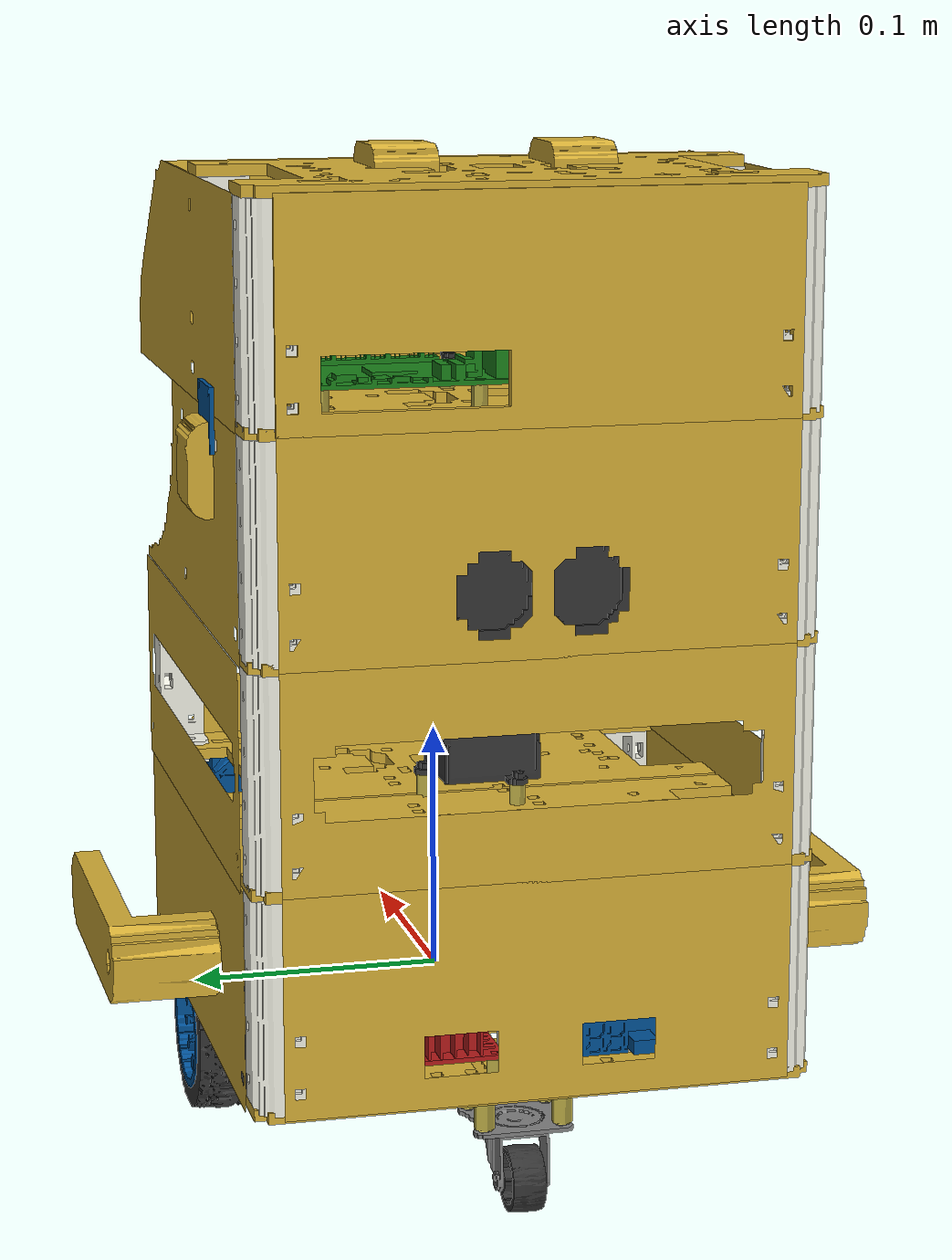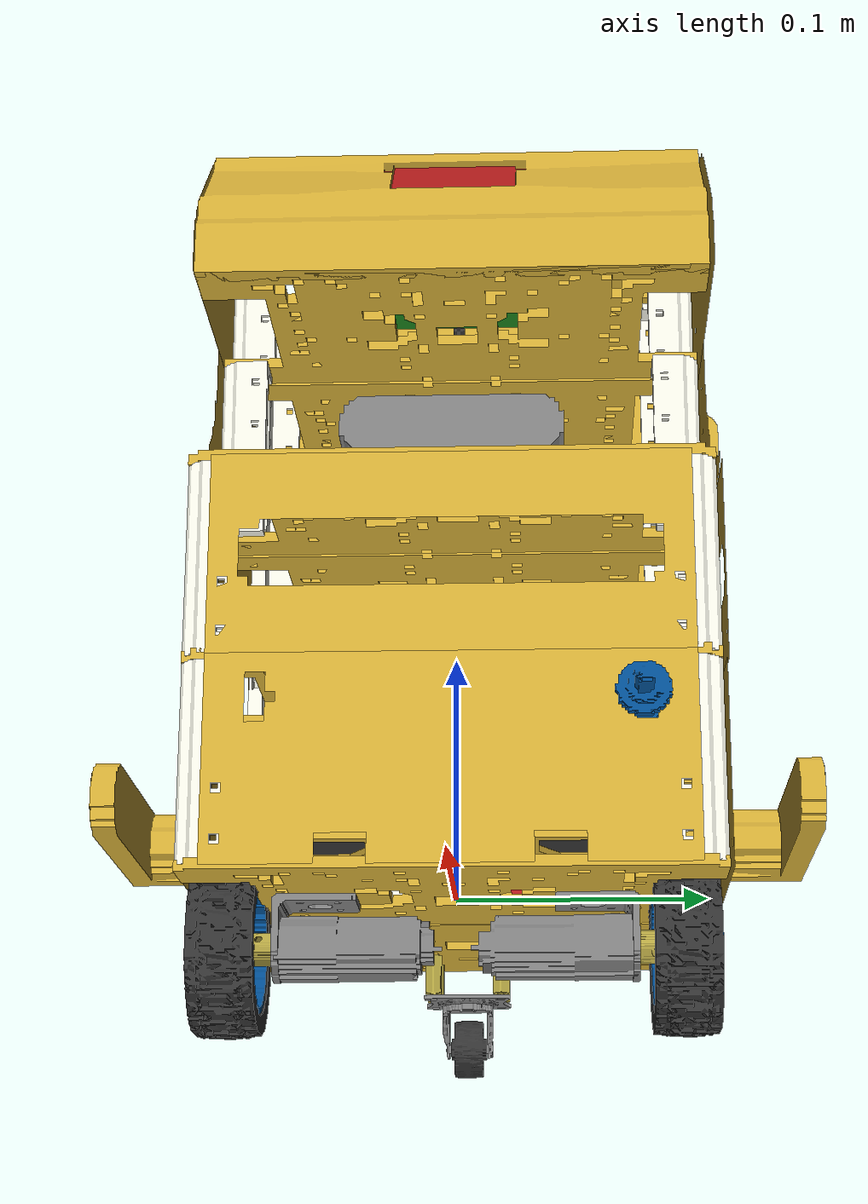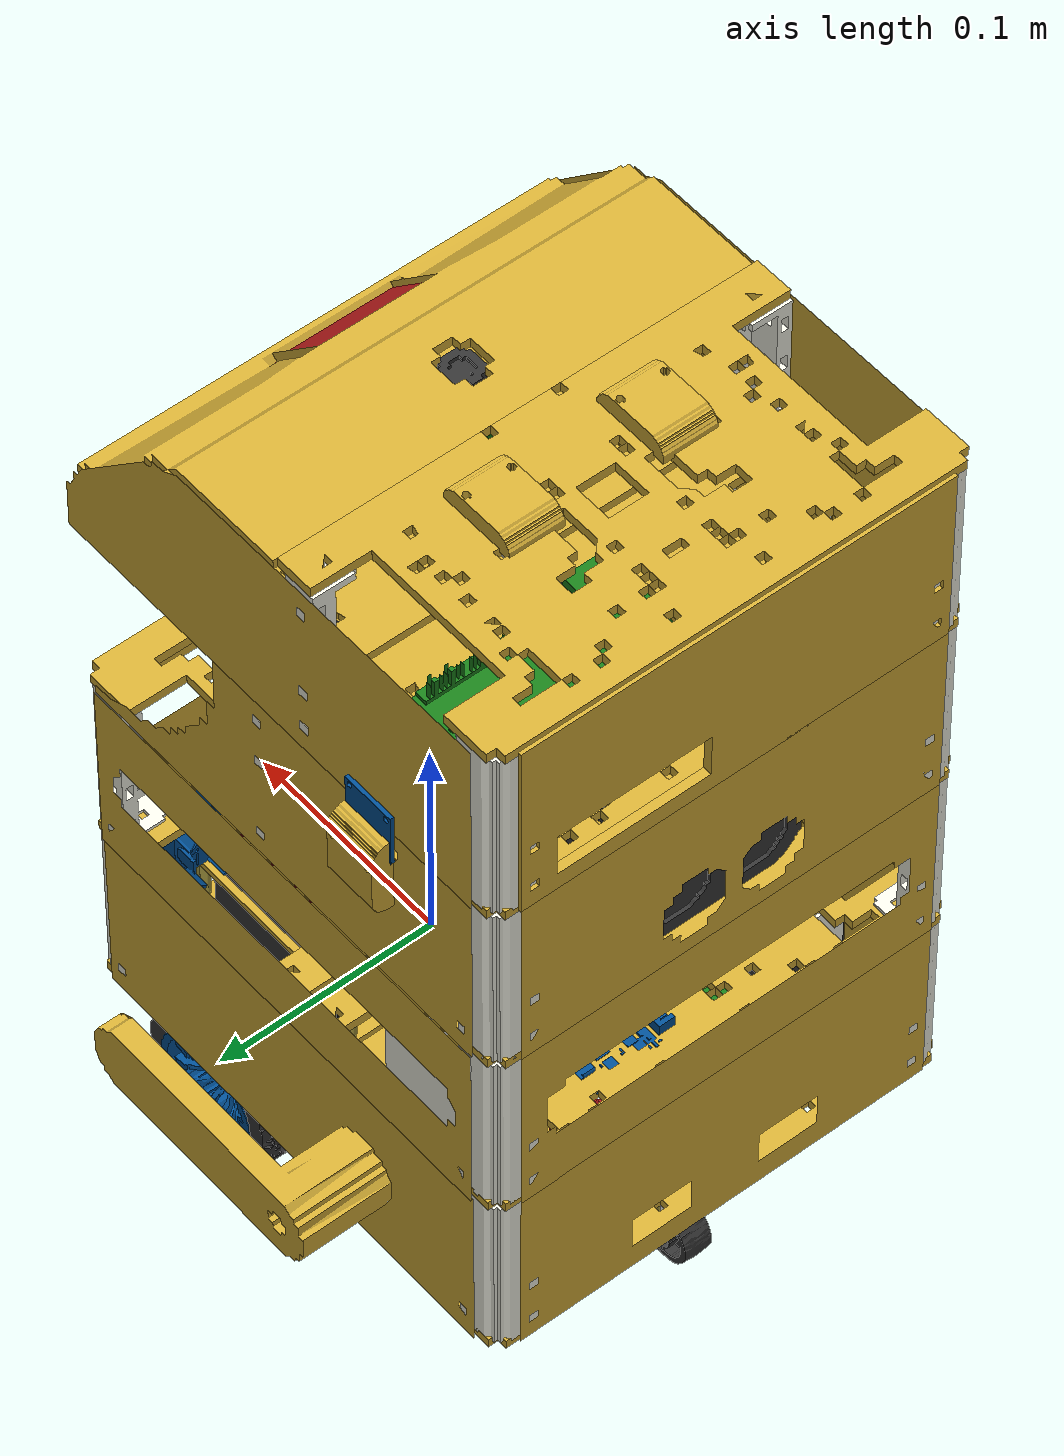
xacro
<?xml version="1.0"?>

<robot xmlns:xacro="http://www.ros.org/wiki/xacro" name="orion">

    <!-- Configurable arguments -->
    <xacro:arg name="camera" default="os30a"/>
    <xacro:arg name="servo" default="true"/>
    <xacro:arg name="g_mov" default="false"/>
    <xacro:arg name="rasp" default="rpi5"/>
    <xacro:arg name="gazebo" default="false"/>
    <xacro:arg name="ros2_control" default="false"/>
    <xacro:arg name="simplified" default="false"/>
    <xacro:arg name="motor" default="100"/>
    <xacro:arg name="ctl_type" default="micro_ros"/>
    <xacro:arg name="color" default="gold"/>

    <xacro:property name="camera" default="$(arg camera)"/>
    <xacro:property name="servo" default="$(arg servo)"/>
    <xacro:property name="g_mov" default="$(arg g_mov)"/>
    <xacro:property name="rasp" default="$(arg rasp)"/>
    <xacro:property name="gazebo" default="$(arg gazebo)"/>
    <xacro:property name="ros2_control" default="$(arg ros2_control)"/>
    <xacro:property name="simplified" default="$(arg simplified)"/>
    <xacro:property name="motor" default="$(arg motor)"/>
    <xacro:property name="ctl_type" default="$(arg ctl_type)"/>

    <!-- Visual color for structural panels: 'mdf', 'transparent', 'pla', 'gold' -->
    <xacro:property name="color" default="$(arg color)"/>

    <!-- Include other files for robot description -->
    <xacro:include filename="$(find orion_description)/urdf/include/orion_materials.urdf.xacro"/>
    <xacro:include filename="$(find orion_description)/urdf/include/orion_macros.urdf.xacro"/>
    <xacro:include filename="$(find orion_description)/urdf/include/orion_g_mov.urdf.xacro"/>
    <xacro:include filename="$(find orion_description)/urdf/include/orion_base.urdf.xacro"/>
    <xacro:include filename="$(find orion_description)/urdf/include/orion_arms.urdf.xacro"/>
    <xacro:include filename="$(find orion_description)/urdf/include/orion_cameras.urdf.xacro"/>
    <xacro:include filename="$(find orion_description)/urdf/include/orion_ros2_control.urdf.xacro"/>

</robot>

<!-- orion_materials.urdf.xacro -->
<!-- @file orion_materials.urdf.xacro
     @brief Material and color definitions used across the ORION URDF. -->
<robot xmlns:xacro="http://www.ros.org/wiki/xacro">

    <!-- Equivalent to RGB(0, 79, 148) -->
    <material name="ArduinoBlue">
        <color rgba="0.0 0.31 0.58 1.0"/>
    </material>

    <!-- Equivalent to RGB(26, 127, 26) -->
    <material name="RaspberryGreen">
        <color rgba="0.1 0.5 0.1 1.0"/>
    </material>

    <!-- Equivalent to RGB(179, 26, 26) -->
    <material name="DriverRed">
        <color rgba="0.7 0.1 0.1 1.0"/>
    </material>

    <!-- Equivalent to RGB(26, 26, 26) -->
    <material name="SoftBlack">
        <color rgba="0.2 0.2 0.2 1.0"/>
    </material>

    <!-- Equivalent to RGB(255, 255, 255) -->
    <material name="PureWhite">
        <color rgba="1.0 1.0 1.0 1.0"/>
    </material>

    <!-- Equivalent to RGB(240, 240, 225) -->
    <material name="PLAWhite">
        <color rgba="0.95 0.95 0.90 1.0"/>
    </material>

    <!-- Equivalent to RGB(181, 165, 66) -->
    <material name="Brass">
        <color rgba="0.71 0.65 0.26 1.0"/>
    </material>

    <!-- Equivalent to RGB(212, 173, 54) -->
    <material name="Gold">
        <color rgba="0.83 0.68 0.21 1.0"/>
    </material>

    <!-- Equivalent to RGB(128, 128, 128) -->
    <material name="MetalGray">
        <color rgba="0.5 0.5 0.5 1.0"/>
    </material>

    <!-- Equivalent to RGB(39, 39, 39) -->
    <material name="TransparentBlack">
        <color rgba="0.3 0.3 0.3 0.8"/>
    </material>

    <!-- Equivalent to RGB(141, 141, 141) -->
    <material name="PLAGray">
        <color rgba="0.6 0.6 0.6 1.0"/>
    </material>

    <!-- Equivalent to RGB(187, 133, 89) -->
    <material name="MDF">
        <color rgba="0.72 0.52 0.35 1.0"/>
    </material>

    <!-- Selects the visual material for structural panels based on the global
         ${color} property. Supported values: 'mdf', 'transparent', 'pla', 'gold'. -->
    <xacro:macro name="apply_color_material">
        <xacro:if value="${color == 'mdf'}">
            <material name="MDF"/>
        </xacro:if>
        <xacro:if value="${color == 'transparent'}">
            <material name="TransparentBlack"/>
        </xacro:if>
        <xacro:if value="${color == 'pla'}">
            <material name="PLAWhite"/>
        </xacro:if>
        <xacro:if value="${color == 'gold'}">
            <material name="Gold"/>
        </xacro:if>
    </xacro:macro>

</robot>

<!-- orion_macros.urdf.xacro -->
<robot xmlns:xacro="http://www.ros.org/wiki/xacro">

    <!--//////////////////// MATH AND NUMS MACROS ///////////////////////-->

    <xacro:property name="pi_2" value="${pi / 2}"/>
    <xacro:property name="pi_4" value="${pi / 4}"/>
    <xacro:property name="pi_6" value="${pi / 6}"/>
    <xacro:property name="pi_8" value="${pi / 8}"/>

    <!--/////////////////// GAZEBO FRICTION MACROS //////////////////////-->

    <!-- Standard Coulomb friction tags emitted only when ${gazebo} is true.
         Defaults match the most common case (mu1=mu2=1.0). -->
    <xacro:macro name="gazebo_friction" params="link mu1:=1.0 mu2:=1.0">
        <xacro:if value="${gazebo}">
            <gazebo reference="${link}">
                <mu1>${mu1}</mu1>
                <mu2>${mu2}</mu2>
            </gazebo>
        </xacro:if>
    </xacro:macro>

    <!-- Friction + contact stiffness (kp) and damping (kd). Used for rolling
         contacts (caster wheel/middle) where contact dynamics matter. -->
    <xacro:macro name="gazebo_friction_contact" params="link mu1 mu2 kp kd">
        <xacro:if value="${gazebo}">
            <gazebo reference="${link}">
                <mu1>${mu1}</mu1>
                <mu2>${mu2}</mu2>
                <kp>${kp}</kp>
                <kd>${kd}</kd>
            </gazebo>
        </xacro:if>
    </xacro:macro>

    <!-- Friction for sensor links that should not self-collide. -->
    <xacro:macro name="gazebo_friction_sensor" params="link mu1:=0.05 mu2:=0.05">
        <xacro:if value="${gazebo}">
            <gazebo reference="${link}">
                <selfCollide>false</selfCollide>
                <mu1>${mu1}</mu1>
                <mu2>${mu2}</mu2>
            </gazebo>
        </xacro:if>
    </xacro:macro>

    <!--///////////////////// 10 x 80 SPACERS MACROS ///////////////////////-->

    <!-- ......................... Single custom spacer ................... -->
    <xacro:macro name="spacer_10x80" params="front side level x y z">
        <!-- Orientation properties -->
        <xacro:property name="muls" value="1"/>
        <xacro:if value="${side == 2}">
            <xacro:property name="muls" value="-1"/>
        </xacro:if>
        <xacro:property name="mulf" value="1"/>
        <xacro:if value="${front == 2}">
            <xacro:property name="mulf" value="-1"/>
        </xacro:if>
        <xacro:property name="gyro" value="${pi}"/>
        <xacro:if value="${side == 2 and front == 1}">
            <xacro:property name="gyro" value="${pi_2}"/>
        </xacro:if>
        <xacro:if value="${side == 1 and front == 2}">
            <xacro:property name="gyro" value="${3*pi_2}"/>
        </xacro:if>
        <xacro:if value="${side == 2 and front == 2}">
            <xacro:property name="gyro" value="0"/>
        </xacro:if>

        <!-- Link definition-->
        <link name="spacer_l${level}_${front}${side}">
        <visual>
            <origin xyz="0 0 0" rpy="0 0 ${gyro}"/>
            <geometry>
            <mesh filename="package://orion_description/meshes/spacer_10x80.stl"
                scale="0.001 0.001 0.001"/>
            </geometry>
            <material name="PLAWhite"/>
        </visual>
        <collision>
            <origin xyz="0 0 0" rpy="0 0 ${gyro}"/>
            <geometry>
            <mesh filename="package://orion_description/meshes/spacer_10x80.stl"
                scale="0.001 0.001 0.001"/>
            </geometry>
        </collision>
        <inertial>
            <origin xyz="0 0 0" rpy="0 0 ${gyro}"/>
            <mass value="0.012"/>
            <inertia ixx="6.799999999999999e-06" ixy="0.0" ixz="0.0"
                    iyy="6.799999999999999e-06" iyz="0.0"
                    izz="8e-07"/>
        </inertial>
        </link>
        <joint name="spacer_l${level}_${front}${side}_joint" type="fixed">
            <parent link="base_l${level}_s${front}"/>
            <child link="spacer_l${level}_${front}${side}"/>
            <origin xyz="${x*mulf} ${y*muls} ${z+0.0025}" rpy="0 0 0"/>
        </joint>
        <xacro:gazebo_friction link="spacer_l${level}_${front}${side}"/>
    </xacro:macro>

    <!-- ....................... Double 10x80 Spacer .................... -->
    <xacro:macro name="double_spacer_10x80" params="front level x y z">
        <xacro:spacer_10x80 front="${front}" side="1" level="${level}" x="${x}"
            y="${y}" z="${z}"/>
        <xacro:spacer_10x80 front="${front}" side="2" level="${level}" x="${x}"
            y="${y}" z="${z}"/>
    </xacro:macro>

    <!--//////////////////// BASES AND LEVELS MACROS ///////////////////////-->

    <!-- ................... Half base macro .............................. -->
    <xacro:macro name="half_base" params="level side parent x y z">
        <xacro:property name="mul" value="1"/>
        <xacro:if value="${side == 2}">
            <xacro:property name="mul" value="-1"/>
        </xacro:if>
        <link name="base_l${level}_s${side}">
        <visual>
            <origin xyz="0 0 0" rpy="0 0 ${mul*pi_2}"/>
            <geometry>
            <mesh filename="package://orion_description/meshes/half_platform.stl"
                scale="0.001 0.001 0.001"/>
            </geometry>
            <xacro:apply_color_material/>
        </visual>
        <collision>
            <origin xyz="0 0 0" rpy="0 0 ${mul*pi_2}"/>
            <geometry>
            <mesh filename="package://orion_description/meshes/half_platform.stl"
                scale="0.001 0.001 0.001"/>
            </geometry>
        </collision>
        <inertial>
            <origin xyz="0 0 0" rpy="0 0 ${mul*pi_2}"/>
            <mass value="0.053"/>
            <inertia ixx="5.843802083333332e-05" ixy="0.0" ixz="0.0"
                    iyy="0.00019480260416666664" iyz="0.0"
                    izz="0.0002531854166666666"/>
        </inertial>
        </link>
        <joint name="base_l${level}_s${side}_joint" type="fixed">
            <parent link="${parent}"/>
            <child link="base_l${level}_s${side}"/>
            <origin xyz="${x + (mul*0.115/2)} ${y} ${z}" rpy="0 0 0"/>
        </joint>
        <xacro:gazebo_friction link="base_l${level}_s${side}"/>
    </xacro:macro>

    <!-- ...................... Complete base ............................ -->
    <xacro:macro name="com_base" params="level parent x y z">
        <xacro:half_base level="${level}" side="1" parent="middle_base" x="${x}"
            y="${y}" z="${z}"/>
        <xacro:half_base level="${level}" side="2" parent="middle_base" x="${x}"
            y="${y}" z="${z}"/>
    </xacro:macro>

    <!--  /////////////////// MOTOR DC MACROS ///////////////////////////////-->
    <!-- ....................... Motor DC Kit .............................. -->
    <xacro:macro name="motor_dc" params="front side x y z">
        <!-- Properties -->
        <xacro:property name="mulf" value="1"/>
        <xacro:if value="${front == 2}">
            <xacro:property name="mulf" value="-1"/>
        </xacro:if>
        <xacro:property name="muls" value="1"/>
        <xacro:property name="orin" value="0"/>
        <xacro:if value="${side == 2}">
            <xacro:property name="muls" value="-1"/>
            <xacro:property name="orin" value="${pi}"/>
        </xacro:if>
        <!-- Motor mount definition-->
        <link name="motor_support_${front}${side}">
        <visual>
            <origin xyz="0 0 0" rpy="${pi} 0 ${orin}"/>
            <geometry>
            <mesh filename="package://orion_description/meshes/motor_mount.stl"
                scale="0.001 0.001 0.001"/>
            </geometry>
            <material name="MetalGray"/>
        </visual>
        <collision>
            <origin xyz="0 0 0" rpy="${pi} 0 ${orin}"/>
            <geometry>
            <mesh filename="package://orion_description/meshes/motor_mount.stl"
                scale="0.001 0.001 0.001"/>
            </geometry>
        </collision>
        <inertial>
            <origin xyz="0 0 0" rpy="${pi} 0 ${orin}"/>
            <mass value="0.011753"/>
            <inertia ixx="2.1329054208642935e-06" ixy="0.0" ixz="0.0"
                    iyy="1.7437733457263675e-06" iyz="0.0"
                    izz="1.7440374248620737e-06"/>
        </inertial>
        </link>
        <joint name="motor_support_${front}${side}_joint" type="fixed">
            <parent link="base_l0_s${front}"/>
            <child link="motor_support_${front}${side}"/>
            <origin xyz="${x*mulf} ${y*muls} ${z+0.0025}" rpy="0 0 0"/>
        </joint>
        <xacro:gazebo_friction link="motor_support_${front}${side}"/>

        <!-- Link motor dc definition-->
        <link name="motor_dc_${front}${side}">
        <visual>
            <origin xyz="0 0 0" rpy="${-pi_2*muls} 0 0"/>
            <geometry>
            <mesh filename="package://orion_description/meshes/motor_dc.stl"
                scale="0.001 0.001 0.001"/>
            </geometry>
            <material name="MetalGray"/>
        </visual>
        <collision>
            <origin xyz="0 0 0" rpy="${-pi_2*muls} 0 0"/>
            <geometry>
            <mesh filename="package://orion_description/meshes/motor_dc.stl"
                scale="0.001 0.001 0.001"/>
            </geometry>
        </collision>
        <inertial>
            <origin xyz="0 0 0" rpy="${-pi_2*muls} 0 0"/>
            <mass value="0.099"/>
            <inertia ixx="5.612122306673401e-05" ixy="0.0" ixz="0.0"
                    iyy="5.6124427915649726e-05" iyz="0.0"
                    izz="1.0309295151084287e-05"/>
        </inertial>
        </link>
        <joint name="motor_dc_${front}${side}_joint" type="fixed">
            <parent link="motor_support_${front}${side}"/>
            <child link="motor_dc_${front}${side}"/>
            <origin xyz="0 ${-0.05625*muls} 0" rpy="0 0 0"/>
        </joint>
        <xacro:gazebo_friction link="motor_dc_${front}${side}"/>

        <!-- Coupling definition-->
        <link name="coupling_${front}${side}">
        <visual>
            <origin xyz="0 0 0" rpy="${orin} 0 ${pi_6*muls}"/>
            <geometry>
            <mesh filename="package://orion_description/meshes/coupling.stl"
                scale="0.001 0.001 0.001"/>
            </geometry>
            <material name="Brass"/>
        </visual>
        <collision>
            <origin xyz="0 0 0" rpy="${orin} 0 ${pi_6*muls}"/>
            <geometry>
            <mesh filename="package://orion_description/meshes/coupling.stl"
                scale="0.001 0.001 0.001"/>
            </geometry>
        </collision>
        <inertial>
            <origin xyz="0 0 0" rpy="${orin} 0 ${pi_6*muls}"/>
            <mass value="0.0152"/>
            <inertia ixx="6.244666666666666e-07" ixy="0.0" ixz="0.0"
                    iyy="6.958222391764178e-07" iyz="0.0"
                    izz="4.994889058430845e-07"/>
        </inertial>
        </link>
        <joint name="coupling_${front}${side}_joint" type="continuous">
            <axis xyz="0.0 0.0 1.0"/>
            <parent link="motor_support_${front}${side}"/>
            <child link="coupling_${front}${side}"/>
            <xacro:if value="${motor == 1000}">
                <limit effort="0.01079" velocity="104.97"/>
            </xacro:if>
            <xacro:if value="${motor == 100}">
                <limit effort="0.08336" velocity="10.47"/>
            </xacro:if>
            <origin xyz="0 ${(0.01120 + 0.000325)*muls} 0" rpy="${-pi_2*muls+orin} 0 0"/>
        </joint>
        <xacro:gazebo_friction link="coupling_${front}${side}"/>

        <!-- Ring definition -->
        <link name="ring_${front}${side}">
        <visual>
            <origin xyz="0 0 0" rpy="0 ${-pi_2*muls} 0"/>
            <geometry>
            <mesh filename="package://orion_description/meshes/ring.stl"
                scale="0.001 0.001 0.001"/>
            </geometry>
            <material name="ArduinoBlue"/>
        </visual>
        <collision>
            <origin xyz="0 0 0" rpy="0 ${-pi_2*muls} 0"/>
            <geometry>
            <mesh filename="package://orion_description/meshes/ring.stl"
                scale="0.001 0.001 0.001"/>
            </geometry>
        </collision>
        <inertial>
            <origin xyz="0 0 0" rpy="0 ${-pi_2*muls} 0"/>
            <mass value="0.0109"/>
            <inertia ixx="4.816756860757923e-06" ixy="0.0" ixz="0.0"
                    iyy="2.9882463541666663e-06" iyz="0.0"
                    izz="2.9867490482579234e-06"/>
        </inertial>
        </link>
        <joint name="ring_${front}${side}_joint" type="fixed">
            <parent link="coupling_${front}${side}"/>
            <child link="ring_${front}${side}"/>
            <origin xyz="0 0 ${0.0068*muls}" rpy="0 0 0"/>
        </joint>
        <xacro:gazebo_friction link="ring_${front}${side}"/>

        <!-- Neumatic definition-->
        <link name="neumatic_${front}${side}">
        <visual>
            <origin xyz="0 0 0" rpy="0 ${pi_2*muls} 0"/>
            <geometry>
            <mesh filename="package://orion_description/meshes/neumatic.stl"
                scale="0.001 0.001 0.001"/>
            </geometry>
            <material name="SoftBlack"/>
        </visual>
        <collision>
            <origin xyz="0 0 0" rpy="0 ${pi_2*muls} 0"/>
            <geometry>
            <sphere radius="0.033675"/>
            <!--mesh filename="package://orion_description/meshes/neumatic.stl"
                scale="0.001 0.001 0.001"/-->
            </geometry>
        </collision>
        <inertial>
            <origin xyz="0 0 0" rpy="0 ${pi_2*muls} 0"/>
            <mass value="0.0399"/>
            <inertia ixx="3.15394093727487e-05" ixy="0.0" ixz="0.0"
                    iyy="1.7872841935074492e-05" iyz="0.0"
                    izz="1.7872841935074492e-05"/>
        </inertial>
        </link>
        <joint name="neumatic_${front}${side}_joint" type="fixed">
            <parent link="ring_${front}${side}"/>
            <child link="neumatic_${front}${side}"/>
            <origin xyz="0 0 0" rpy="0 0 0"/>
        </joint>
        <xacro:gazebo_friction link="neumatic_${front}${side}" mu1="1.0" mu2="0.8"/>

    </xacro:macro>

    <!--////////////////////////// CASTER WHEEL ////////////////////////////-->
    <xacro:property name="caster_type" value="fixed"/>

    <xacro:if value="${gazebo}">
        <xacro:property name="caster_type" value="continuous"/>
    </xacro:if>

    <!-- ......................... Macro for caster ....................... -->
    <xacro:macro name="caster_wheel" params="parent front x y z">
        <!-- Caster base definition-->
        <link name="caster_base_${front}">
        <visual>
            <origin xyz="0 0 0" rpy="${pi} 0 ${pi_2}"/>
            <geometry>
            <mesh filename="package://orion_description/meshes/caster_base.stl"
                scale="0.001 0.001 0.001"/>
            </geometry>
            <material name="MetalGray"/>
        </visual>
        <collision>
            <origin xyz="0 0 0" rpy="${pi} 0 ${pi_2}"/>
            <geometry>
            <mesh filename="package://orion_description/meshes/caster_base.stl"
                scale="0.001 0.001 0.001"/>
            </geometry>
        </collision>
        <inertial>
            <origin xyz="0 0 0" rpy="${pi} 0 ${pi_2}"/>
            <mass value="0.01085"/>
            <inertia ixx="9.360136765056053e-07" ixy="0.0" ixz="0.0"
                    iyy="1.315763414372338e-06" iyz="0.0"
                    izz="2.2314830712000656e-06"/>
        </inertial>
        </link>
        <joint name="caster_base_${front}_joint" type="fixed">
            <parent link="${parent}"/>
            <child link="caster_base_${front}"/>
            <origin xyz="${x} ${y} ${z}" rpy="0 0 0"/>
        </joint>
        <xacro:gazebo_friction link="caster_base_${front}"/>

        <!-- Caster middle definition-->
        <link name="caster_middle_${front}">
        <visual>
            <origin xyz="0 0 0" rpy="0 0 ${-pi_2}"/>
            <geometry>
            <mesh filename="package://orion_description/meshes/caster_middle.stl"
                scale="0.001 0.001 0.001"/>
            </geometry>
            <material name="MetalGray"/>
        </visual>
        <collision>
            <origin xyz="0 0 0" rpy="0 0 ${-pi_2}"/>
            <geometry>
            <mesh filename="package://orion_description/meshes/caster_middle.stl"
                scale="0.001 0.001 0.001"/>
            </geometry>
        </collision>
        <inertial>
            <origin xyz="0 0 0" rpy="0 0 ${-pi_2}"/>
            <mass value="0.001"/>
            <inertia ixx="1.6321007868011535e-06" ixy="0.0" ixz="0.0"
                    iyy="1.3901075509910613e-06" iyz="0.0"
                    izz="1.644364587792215e-06"/>
        </inertial>
        </link>
        <joint name="caster_middle_${front}_joint" type="${caster_type}">
            <axis xyz="0.0 0.0 1.0"/>
            <parent link="caster_base_${front}"/>
            <child link="caster_middle_${front}"/>
            <origin xyz="0 0 -0.002" rpy="${pi} 0 0"/>
            <dynamics damping="0.05" friction="0.0"/>
        </joint>
        <xacro:gazebo_friction_contact link="caster_middle_${front}"
            mu1="0.01" mu2="0.01" kp="100000.0" kd="10.0"/>

        <!-- Caster wheel definition-->
        <link name="caster_wheel_${front}">
        <visual>
            <origin xyz="0 0 0" rpy="${pi_2} 0 0"/>
            <geometry>
            <mesh filename="package://orion_description/meshes/caster_wheel.stl"
                scale="0.001 0.001 0.001"/>
            </geometry>
            <material name="SoftBlack"/>
        </visual>
        <collision>
            <origin xyz="0 0 0" rpy="${pi_2} 0 0"/>
            <geometry>
            <mesh filename="package://orion_description/meshes/caster_wheel.stl"
                scale="0.001 0.001 0.001"/>
            </geometry>
        </collision>
        <inertial>
            <origin xyz="0 0 0" rpy="${pi_2} 0 0"/>
            <mass value="0.001"/>
            <inertia ixx="5.723473258925721e-07" ixy="0.0" ixz="0.0"
                    iyy="8.268436933141506e-07" iyz="0.0"
                    izz="5.724272007549117e-07"/>
        </inertial>
        </link>
        <joint name="caster_wheel_${front}_joint" type="${caster_type}">
            <axis xyz="0.0 0.0 1.0"/>
            <parent link="caster_middle_${front}"/>
            <child link="caster_wheel_${front}"/>
            <origin xyz="-0.0108 0 0.0185" rpy="${pi_2} 0 0"/>
            <dynamics damping="0.05" friction="0.0"/>
        </joint>
        <xacro:gazebo_friction_contact link="caster_wheel_${front}"
            mu1="0.01" mu2="0.01" kp="100000.0" kd="10.0"/>
    </xacro:macro>

    <!-- ///////////////////// BATTERIES MACROS ////////////////////////////-->
    <!-- ...................... B18650 Macro .............................. -->
    <xacro:macro name="b18650" params="parent element num x y z">
        <xacro:property name="inv" value="1"/>
        <xacro:property name="rot" value="${pi_2}"/>
        <xacro:if value="${num == 2}">
            <xacro:property name="rot" value="${pi_2*3}"/>
            <xacro:property name="inv" value="-1"/>
        </xacro:if>
        <xacro:if value="${num == 3}">
            <xacro:property name="rot" value="${pi_2*5}"/>
        </xacro:if>
        <!-- Link -->
        <link name="${element}_${num}">
        <visual>
            <origin xyz="0 0 0" rpy="0 ${rot} 0"/>
            <geometry>
            <mesh filename="package://orion_description/meshes/b18650.stl"
                scale="0.001 0.001 0.001"/>
            </geometry>
            <material name="DriverRed"/>
        </visual>
        <collision>
            <origin xyz="0 0 0" rpy="0 ${rot} 0"/>
            <geometry>
            <mesh filename="package://orion_description/meshes/b18650.stl"
                scale="0.001 0.001 0.001"/>
            </geometry>
        </collision>
        <inertial>
            <origin xyz="0 0 0"/>
            <mass value="0.048"/>
            <inertia ixx="1.9520194552672923e-06" ixy="0.0" ixz="0.0"
                    iyy="1.9520999999999995e-06" iyz="0.0"
                    izz="2.5911945526729246e-07"/>
        </inertial>
        </link>
        <joint name="${element}_${num}_joint" type="fixed">
            <parent link="${parent}"/>
            <child link="${element}_${num}"/>
            <origin xyz="${x*inv} ${y} ${z}" rpy="0 0 0"/>
        </joint>
        <xacro:gazebo_friction link="${element}_${num}"/>
    </xacro:macro>

    <!-- ........................ Battery holder macro ........................ -->
    <xacro:macro name="bat_hold" params="parent element num x y z">
        <!-- Link -->
        <link name="${element}_${num}">
        <visual>
            <origin xyz="0 0 0" rpy="0 0 ${pi_2}"/>
            <geometry>
            <mesh filename="package://orion_description/meshes/batteryholderx3.stl"
                scale="0.001 0.001 0.001"/>
            </geometry>
            <material name="SoftBlack"/>
        </visual>
        <collision>
            <origin xyz="0 0 0" rpy="0 0 ${pi_2}"/>
            <geometry>
            <mesh filename="package://orion_description/meshes/batteryholderx3.stl"
                scale="0.001 0.001 0.001"/>
            </geometry>
        </collision>
        <inertial>
            <origin xyz="0 0 0" rpy="0 0 ${pi_2}"/>
            <mass value="0.02012"/>
            <inertia ixx="1.4044179166666666e-06" ixy="0.0" ixz="0.0"
                    iyy="2.9665263333333333e-06" iyz="0.0"
                    izz="4.369602916666666e-06"/>
        </inertial>
        </link>
        <joint name="${element}_${num}_joint" type="fixed">
            <parent link="${parent}"/>
            <child link="${element}_${num}"/>
            <origin xyz="${x} ${y} ${z}" rpy="0 0 0"/>
        </joint>
        <xacro:gazebo_friction link="${element}_${num}"/>
    </xacro:macro>

    <xacro:macro name="stack_bat" params="parent num x y z">
        <xacro:property name="serie" value="0.009"/>
        <xacro:bat_hold parent="${parent}" element="bathold" num="${num}"
            x="${x}" y="${y}" z="${z}"/>
        <xacro:b18650 parent="bathold_${num}" element="b18650_${num}" num="1"
            x="${-0.065/2}" y="${serie}" z="0.01"/>
        <xacro:b18650 parent="bathold_${num}" element="b18650_${num}" num="2"
            x="${-0.065/2}" y="${-serie}" z="0.01"/>
        <xacro:b18650 parent="bathold_${num}" element="b18650_${num}" num="3"
            x="${-0.065/2}" y="${-serie*3}" z="0.01"/>
    </xacro:macro>

    <!-- //////////////////// SERVOS MACROS ///////////////////////////////-->

    <xacro:macro name="servo_mounted" params="parent side x y z">
        <!-- Servo Mount Link -->
        <xacro:property name="inv" value="1"/>
        <xacro:property name="flex" value="0"/>
        <xacro:if value="${side == 2}">
            <xacro:property name="inv" value="-1"/>
            <xacro:property name="flex" value="${pi}"/>
        </xacro:if>
        <link name="servo_support_${side}">
        <visual>
            <origin xyz="0 0 0" rpy="${-pi_2} 0 ${flex}"/>
            <geometry>
            <mesh filename="package://orion_description/meshes/servo_sup.stl"
                scale="0.001 0.001 0.001"/>
            </geometry>
            <material name="PLAWhite"/>
        </visual>
        <collision>
            <origin xyz="0 0 0" rpy="${-pi_2} 0 ${flex}"/>
            <geometry>
            <mesh filename="package://orion_description/meshes/servo_sup.stl"
                scale="0.001 0.001 0.001"/>
            </geometry>
        </collision>
        <inertial>
            <origin xyz="0 0 0" rpy="${-pi_2} 0 ${flex}"/>
            <mass value="0.012"/>
            <inertia ixx="3.1172499999999997e-06" ixy="0.0" ixz="0.0"
                    iyy="4.2049999999999996e-06" iyz="0.0"
                    izz="6.60025e-06"/>
        </inertial>
        </link>
        <joint name="servo_support_${side}_joint" type="fixed">
            <parent link="${parent}"/>
            <child link="servo_support_${side}"/>
            <origin xyz="${x} ${y*inv} ${z}" rpy="0 0 0"/>
        </joint>
        <xacro:gazebo_friction link="servo_support_${side}"/>
        <!-- Servo Link -->
        <link name="servo_${side}">
        <visual>
            <origin xyz="0 0 0" rpy="${-pi_2*inv} 0 0"/>
            <geometry>
            <mesh filename="package://orion_description/meshes/mg996r.stl"
                scale="0.001 0.001 0.001"/>
            </geometry>
            <material name="SoftBlack"/>
        </visual>
        <collision>
            <origin xyz="0 0 0" rpy="${-pi_2*inv} 0 0"/>
            <geometry>
            <mesh filename="package://orion_description/meshes/mg996r.stl"
                scale="0.001 0.001 0.001"/>
            </geometry>
        </collision>
        <inertial>
            <origin xyz="0 0 0" rpy="${-pi_2*inv} 0 0"/>
            <mass value="0.055"/>
            <inertia ixx="1.1155878535842904e-05" ixy="0.0" ixz="0.0"
                    iyy="2.1057527828089415e-05" iyz="0.0"
                    izz="1.3568315958913178e-05"/>
        </inertial>
        </link>
        <joint name="servo_${side}_joint" type="fixed">
            <parent link="servo_support_${side}"/>
            <child link="servo_${side}"/>
            <origin xyz="0 ${-0.0216*inv} -0.01375" rpy="0 0 0"/>
        </joint>
        <xacro:gazebo_friction link="servo_${side}" mu1="0.05" mu2="0.05"/>
        <!-- Servo Conn -->
        <link name="servo_conn_${side}">
        <visual>
            <origin xyz="0 0 0" rpy="0 0 0"/>
            <geometry>
            <mesh filename="package://orion_description/meshes/servo_conn.stl"
                scale="0.001 0.001 0.001"/>
            </geometry>
            <material name="MetalGray"/>
        </visual>
        <collision>
            <origin xyz="0 0 0" rpy="0 0 0"/>
            <geometry>
            <mesh filename="package://orion_description/meshes/servo_conn.stl"
                scale="0.001 0.001 0.001"/>
            </geometry>
        </collision>
        <inertial>
            <origin xyz="0 0 0" rpy="0 0 0"/>
            <mass value="0.005"/>
            <inertia ixx="1.750719658194081e-07" ixy="0.0" ixz="0.0"
                    iyy="1.750397680831338e-07" iyz="0.0"
                    izz="3.332367339025419e-07"/>
        </inertial>
        </link>
        <joint name="servo_conn_${side}_joint" type="revolute">
            <axis xyz="0.0 0.0 1.0"/>
            <parent link="servo_${side}"/>
            <child link="servo_conn_${side}"/>
            <origin xyz="0.01 ${0.0406*inv} 0" rpy="${-pi_2*inv} 0 0"/>
            <limit lower="${-pi/3}" upper="${pi/3}" effort="1.08" velocity="5.24"/>
            <dynamics damping="0.05" friction="0.002"/>
        </joint>
        <xacro:gazebo_friction link="servo_conn_${side}" mu1="0.05" mu2="0.05"/>
    </xacro:macro>
    <!--///////////////////// SPEAKERS MACROS ///////////////////////-->

    <!-- Speakers Macro -->
    <xacro:macro name="speakers_mount" params="parent front side x y z">
        <!--  Properties -->
        <xacro:property name="mulf" value="1"/>
        <xacro:property name="muls" value="1"/>
        <xacro:property name="inv" value="${pi}"/>
        <xacro:if value="${front == 2}">
            <xacro:property name="mulf" value="-1"/>
        </xacro:if>
        <xacro:if value="${side == 2}">
            <xacro:property name="muls" value="-1"/>
            <xacro:property name="inv" value="0"/>
        </xacro:if>
        <!-- Speaker support -->
        <link name="speaker_sup_${front}${side}">
        <visual>
            <origin xyz="0 0 0" rpy="0 0 ${inv}"/>
            <geometry>
            <mesh filename="package://orion_description/meshes/speaker_sup.stl"
                scale="0.001 0.001 0.001"/>
            </geometry>
            <material name="PLAWhite"/>
        </visual>
        <collision>
            <origin xyz="0 0 0" rpy="0 0 ${inv}"/>
            <geometry>
            <mesh filename="package://orion_description/meshes/speaker_sup.stl"
                scale="0.001 0.001 0.001"/>
            </geometry>
        </collision>
        <inertial>
            <origin xyz="0 0 0" rpy="0 0 ${inv}"/>
            <mass value="0.007"/>
            <inertia ixx="1.402333333333333e-06" ixy="0.0" ixz="0.0"
                    iyy="2.578333333333333e-06" iyz="0.0"
                    izz="1.2926666666666665e-06"/>
        </inertial>
        </link>
        <joint name="speaker_sup_${front}${side}_joint" type="fixed">
            <parent link="${parent}"/>
            <child link="speaker_sup_${front}${side}"/>
            <origin xyz="${x*mulf} ${y*muls} ${z}" rpy="0 0 0"/>
        </joint>
        <xacro:gazebo_friction link="speaker_sup_${front}${side}"/>

        <!-- Speaker -->
        <link name="speaker_${front}${side}">
        <visual>
            <origin xyz="0 0 0" rpy="0 0 ${inv}"/>
            <geometry>
            <mesh filename="package://orion_description/meshes/speaker.stl"
                scale="0.001 0.001 0.001"/>
            </geometry>
            <material name="SoftBlack"/>
        </visual>
        <collision>
            <origin xyz="0 0 0" rpy="0 0 ${inv}"/>
            <geometry>
            <mesh filename="package://orion_description/meshes/speaker.stl"
                scale="0.001 0.001 0.001"/>
            </geometry>
        </collision>
        <inertial>
            <origin xyz="0 0 0" rpy="0 0 ${inv}"/>
            <mass value="0.0456"/>
            <inertia ixx="1.102e-05" ixy="0.0" ixz="0.0"
                    iyy="1.6081600000000002e-05" iyz="0.0"
                    izz="1.102e-05"/>
        </inertial>
        </link>
        <joint name="speaker_${front}${side}_joint" type="fixed">
            <parent link="speaker_sup_${front}${side}"/>
            <child link="speaker_${front}${side}"/>
            <origin xyz="0 ${0.0375*muls/2} 0" rpy="0 0 0"/>
        </joint>
        <xacro:gazebo_friction link="speaker_${front}${side}"/>
    </xacro:macro>

    <!-- ///////////////////////////// WALL MACROS //////////////////////// -->
    <xacro:macro name="complete_lateral_wall"
            params="id parent side level x y z">
        <xacro:property name="muls" value="1"/>
        <xacro:if value="${side == 2}">
            <xacro:property name="muls" value="-1"/>
        </xacro:if>
        <link name="wall_${id}_${level}_${side}">
        <visual>
            <origin xyz="0 0 0" rpy="0 0 ${pi}"/>
            <geometry>
            <mesh filename="package://orion_description/meshes/wall_${id}.stl"
                scale="0.001 0.001 0.001"/>
            </geometry>
            <xacro:apply_color_material/>
        </visual>
        <collision>
            <origin xyz="0 0 0" rpy="0 0 ${pi}"/>
            <geometry>
            <mesh filename="package://orion_description/meshes/wall_${id}.stl"
                scale="0.001 0.001 0.001"/>
            </geometry>
        </collision>
        <inertial>
            <origin xyz="0 0 0" rpy="0 0 ${pi}"/>
            <mass value="0.042"/>
            <inertia ixx="2.3541875e-05" ixy="0.0" ixz="0.0"
                    iyy="0.000177884" iyz="0.0"
                    izz="0.000154357875"/>
        </inertial>
        </link>
        <joint name="wall_${id}_${level}_${side}_joint" type="fixed">
        <parent link="${parent}"/>
        <child link="wall_${id}_${level}_${side}"/>
        <origin xyz="${x} ${(y+0.00075)*muls} ${z}" rpy="0 0 0"/>
        </joint>
        <xacro:gazebo_friction link="wall_${id}_${level}_${side}"
            mu1="0.05" mu2="0.05"/>
    </xacro:macro>

    <xacro:macro name="complete_front_wall"
            params="id parent front level x z">
        <xacro:property name="mulf" value="1"/>
        <xacro:property name="orz" value="0"/>
        <xacro:if value="${front == 2}">
            <xacro:property name="mulf" value="-1"/>
            <xacro:property name="orz" value="${pi}"/>
        </xacro:if>
        <!-- Link -->
        <link name="wall_${id}_${level}_${front}">
        <visual>
            <origin xyz="0 0 0" rpy="0 0 ${pi_2 + orz}"/>
            <geometry>
            <mesh filename="package://orion_description/meshes/wall_${id}.stl"
                scale="0.001 0.001 0.001"/>
            </geometry>
            <xacro:apply_color_material/>
        </visual>
        <collision>
            <origin xyz="0 0 0" rpy="0 0 ${pi_2 + orz}"/>
            <geometry>
            <mesh filename="package://orion_description/meshes/wall_${id}.stl"
                scale="0.001 0.001 0.001"/>
            </geometry>
        </collision>
        <inertial>
            <origin xyz="0 0 0" rpy="0 0 ${pi_2 + orz}"/>
            <mass value="0.039"/>
            <inertia ixx="2.18603125e-05" ixy="0.0" ixz="0.0"
                    iyy="0.000139178" iyz="0.0"
                    izz="0.00011733231249999999"/>
        </inertial>
        </link>
        <joint name="wall_${id}_${level}_${front}_joint" type="fixed">
        <parent link="${parent}"/>
        <child link="wall_${id}_${level}_${front}"/>
        <origin xyz="${(x+0.00075)*mulf} 0 ${z}" rpy="0 0 0"/>
        </joint>
        <xacro:gazebo_friction link="wall_${id}_${level}_${front}"/>
    </xacro:macro>

    <!-- /////////////////////////// Generic Metric Spacer /////////////////-->
    <xacro:macro name="metric_spacer"
            params="id parent element front side x y z">

        <!-- Link Spacer -->
        <link name="${id}_${element}_${front}${side}">
        <visual>
            <origin xyz="0 0 0" rpy="0 0 0"/>
            <geometry>
            <mesh filename="package://orion_description/meshes/spacer_${id}.stl"
                scale="0.001 0.001 0.001"/>
            </geometry>
            <material name="Brass"/>
        </visual>
        <collision>
            <origin xyz="0 0 0" rpy="0 0 0"/>
            <geometry>
            <mesh filename="package://orion_description/meshes/spacer_${id}.stl"
                scale="0.001 0.001 0.001"/>
            </geometry>
        </collision>
        <inertial>
            <origin xyz="0 0 0 " rpy="0 0 0"/>
            <xacro:if value="${id == 'm4x17'}">
                <mass value="0.00109"/>
                <inertia ixx="3.0393740495491044e-08" ixy="0" ixz="0"
                        iyy="3.129874333045412e-08" iyz="0"
                        izz="3.129874333045412e-08"/>
            </xacro:if>
            <xacro:if value="${id == 'm3x10'}">
                <mass value="0.0008"/>
                <inertia ixx="8.550666163126637e-09" ixy="0" ixz="0"
                        iyy="8.960721799390997e-09" iyz="0"
                        izz="4.443388969597693e-09"/>
            </xacro:if>
            <xacro:if value="${id == 'm3x15'}">
                <mass value="0.0017"/>
                <inertia ixx="5.2825999244689955e-08" ixy="0" ixz="0"
                        iyy="5.4441082699086494e-08" iyz="0"
                        izz="9.66508345439654e-09"/>
            </xacro:if>
            <xacro:if value="${id == 'm3x20'}">
                <mass value="0.0024"/>
                <inertia ixx="8.5251996963501e-08" ixy="0" ixz="0"
                        iyy="8.648216387229408e-08" iyz="0"
                        izz="1.333016690879308e-08"/>
            </xacro:if>
            <xacro:if value="${id == 'm3x6'}">
                <mass value="0.00072"/>
                <inertia ixx="3.9036000675201425e-09" ixy="0" ixz="0"
                        iyy="4.272650140158067e-09" iyz="0"
                        izz="3.9990500726379235e-09"/>
            </xacro:if>
        </inertial>
        </link>
        <!-- Joint Spacer -->
        <joint name="${id}_${element}_${front}${side}_joint" type="fixed">
            <parent link="${parent}"/>
            <child link="${id}_${element}_${front}${side}"/>
            <origin xyz="${x} ${y} ${z}" rpy="0 0 0"/>
        </joint>
        <xacro:gazebo_friction link="${id}_${element}_${front}${side}"/>
    </xacro:macro>

    <!-- 2 symetric hex spacers by considering offset -->
    <xacro:macro name="x2xmetric_spacer"
                params="id element parent offset_y x y z">
        <xacro:metric_spacer id="${id}" parent="${parent}" element="${element}"
            front="" side="r" x="${x}" y="${y - offset_y}" z="${z}"/>
        <xacro:metric_spacer id="${id}" parent="${parent}" element="${element}"
            front="" side="l" x="${x}" y="${y + offset_y}" z="${z}"/>
    </xacro:macro>

    <!-- 3  hex spacers by considering triangle -->
    <xacro:macro name="x3xmetric_spacer"
                params="id element parent offset_x offset_y x y z">
        <xacro:metric_spacer id="${id}" parent="${parent}" element="${element}"
            front="f" side="l" x="${x + offset_x}" y="${y - offset_y}" z="${z}"/>
        <xacro:metric_spacer id="${id}" parent="${parent}" element="${element}"
            front="r" side="l" x="${x - offset_x}" y="${y - offset_y}" z="${z}"/>
        <xacro:metric_spacer id="${id}" parent="${parent}" element="${element}"
            front="" side="r" x="${x}" y="${y + offset_y}" z="${z}"/>
    </xacro:macro>

    <!-- 4  hex spacers by considering mirror offset -->
    <xacro:macro name="x4xmetric_spacer"
                params="id element parent offset_x offset_y x y z">
        <xacro:metric_spacer id="${id}" parent="${parent}" element="${element}"
            front="f" side="r" x="${x + offset_x}" y="${y - offset_y}" z="${z}"/>
        <xacro:metric_spacer id="${id}" parent="${parent}" element="${element}"
            front="f" side="l" x="${x + offset_x}" y="${y + offset_y}" z="${z}"/>
        <xacro:metric_spacer id="${id}" parent="${parent}" element="${element}"
            front="r" side="r" x="${x - offset_x}" y="${y + offset_y}" z="${z}"/>
        <xacro:metric_spacer id="${id}" parent="${parent}" element="${element}"
            front="r" side="l" x="${x - offset_x}" y="${y - offset_y}" z="${z}"/>
    </xacro:macro>

    <!-- 6  hex spacers by considering mirror offset and middles-->
    <xacro:macro name="x6xmetric_spacer"
                params="id element parent offset_x offset_y x y z">
        <xacro:metric_spacer id="${id}" parent="${parent}" element="${element}"
            front="f" side="r" x="${x + offset_x}" y="${y - offset_y}" z="${z}"/>
        <xacro:metric_spacer id="${id}" parent="${parent}" element="${element}"
            front="f" side="l" x="${x + offset_x}" y="${y + offset_y}" z="${z}"/>
        <xacro:metric_spacer id="${id}" parent="${parent}" element="${element}"
            front="r" side="r" x="${x - offset_x}" y="${y + offset_y}" z="${z}"/>
        <xacro:metric_spacer id="${id}" parent="${parent}" element="${element}"
            front="r" side="l" x="${x - offset_x}" y="${y - offset_y}" z="${z}"/>
        <xacro:metric_spacer id="${id}" parent="${parent}" element="${element}"
            front="f" side="" x="${x + offset_x}" y="0" z="${z}"/>
        <xacro:metric_spacer id="${id}" parent="${parent}" element="${element}"
            front="r" side="" x="${x - offset_x}" y="0" z="${z}"/>
    </xacro:macro>

    <!-- ////////////////////// Touch sensors macros //////////////////////-->
    <xacro:macro name="touch_sensor" params="x y z upper side parent prefix">
        <xacro:property name="rotR" value="${-pi_2}"/>
        <xacro:property name="rotP" value="${pi}"/>
        <xacro:property name="rotY" value="0"/>
        <xacro:if value="${side == 2}">
            <xacro:property name="rotR" value="${pi_2}"/>
        </xacro:if>
        <xacro:if value="${upper}">
            <xacro:property name="rotR" value="0"/>
            <xacro:property name="rotP" value="0"/>
            <xacro:property name="rotY" value="${-pi_2}"/>
        </xacro:if>
        <link name="touch_sensor_${prefix}${side}">
            <visual name="">
                <origin xyz="0.0 0.0 0.0" rpy="${rotR} ${rotP} ${rotY}"/>
                <geometry>
                    <mesh filename="package://orion_description/meshes/touch_sensor.stl"
                    scale="0.001 0.001 0.001"/>
                </geometry>
                <material name="ArduinoBlue"/>
            </visual>
            <collision>
                <origin xyz="0.0 0.0 0.0" rpy="${rotR} ${rotP} ${rotY}"/>
                <geometry>
                    <mesh filename="package://orion_description/meshes/touch_sensor.stl"
                    scale="0.001 0.001 0.001"/>
                </geometry>
            </collision>
            <inertial>
                <origin xyz="0.0 0.0 0.0" rpy="${rotR} ${rotP} ${rotY}"/>
                <mass value="0.001984467"/>
                <inertia ixx="1.3218052332160457e-07" ixy="0.0" ixz="0.0"
                         iyy="1.0060793220379826e-07" iyz="0.0"
                         izz="2.2367231024415283e-07"/>
            </inertial>
        </link>
        <joint name="touch_sensor_${prefix}${side}_joint" type="fixed">
            <origin xyz="${x} ${y} ${z}" rpy="0.0 0.0 0.0"/>
            <parent link="${parent}"/>
            <child link="touch_sensor_${prefix}${side}"/>
        </joint>
        <xacro:gazebo_friction link="touch_sensor_${prefix}${side}"/>

        <xacro:property name="rotR" value="0"/>
        <xacro:property name="rotP" value="0"/>
        <xacro:property name="rotY" value="${pi}"/>
        <xacro:property name="offsetZ" value="-0.0065"/>
        <xacro:property name="offsetY" value="0.002"/>
        <xacro:property name="offsetX" value="0"/>
        <xacro:if value="${side == 2}">
            <xacro:property name="rotY" value="0"/>
            <xacro:property name="offsetY" value="-0.002"/>
        </xacro:if>
        <xacro:if value="${upper}">
            <xacro:property name="rotR" value="${-pi_2}"/>
            <xacro:property name="rotP" value="0"/>
            <xacro:property name="rotY" value="${-pi_2}"/>
            <xacro:property name="offsetZ" value="0.00175"/>
            <xacro:property name="offsetY" value="0"/>
            <xacro:property name="offsetX" value="-0.0065"/>
        </xacro:if>
        <link name="touch_sup_${prefix}${side}">
            <visual name="">
                <origin xyz="0 0 0" rpy="${rotR} ${rotP} ${rotY}"/>
                <geometry>
                    <mesh filename="package://orion_description/meshes/touch_sensor_sup.stl"
                    scale="0.001 0.001 0.001"/>
                </geometry>
                <xacro:apply_color_material/>
            </visual>
            <collision>
                <origin xyz="0 0 0" rpy="${rotR} ${rotP} ${rotY}"/>
                <geometry>
                    <mesh filename="package://orion_description/meshes/touch_sensor_sup.stl"
                    scale="0.001 0.001 0.001"/>
                </geometry>
            </collision>
            <inertial>
                <origin xyz="0 0 0" rpy="${rotR} ${rotP} ${rotY}"/>
                <mass value="0.004"/>
                <inertia ixx="4.400208333333333e-07" ixy="0.0" ixz="0.0"
                         iyy="6.019366727956135e-07" iyz="0.0"
                         izz="2.252908394622803e-07"/>
            </inertial>
        </link>
        <joint name="touch_sup_${prefix}${side}_joint" type="fixed">
            <origin xyz="${offsetX} ${offsetY} ${offsetZ}" rpy="0 0 0"/>
            <parent link="touch_sensor_${prefix}${side}"/>
            <child link="touch_sup_${prefix}${side}"/>
        </joint>
        <xacro:gazebo_friction link="touch_sup_${prefix}${side}"/>
    </xacro:macro>

    <!-- /////////////////////// Cameras macros //////////////////////// -->
    <xacro:macro name="camera_sensor" params="x y z R P Y parent">
        <!-- ................... Camera sensors links .................. -->
        <link name="camera_link"/>

        <joint name="camera_joint" type="fixed">
            <origin xyz="${x} ${y} ${z}" rpy="0 0 0"/>
            <parent link="${parent}"/>
            <child link="camera_link"/>
        </joint>

        <link name="camera_link_optical"/>

        <joint name="optical_joint" type="fixed">
            <origin xyz="0 0 0" rpy="${R} ${P} ${Y}"/>
            <parent link="camera_link"/>
            <child link="camera_link_optical"/>
        </joint>
    </xacro:macro>

    <!--//////////////// COMPOSITE / REPEATED UNITS //////////////////////-->

    <xacro:macro name="bat_platform_unit" params="suffix parent x y z">
        <link name="bat_platform${suffix}">
            <visual>
                <origin xyz="0 0 0" rpy="0 0 ${pi_2}"/>
                <geometry>
                    <mesh filename="package://orion_description/meshes/bathold_support.stl"
                        scale="0.001 0.001 0.001"/>
                </geometry>
                <xacro:apply_color_material/>
            </visual>
            <collision>
                <origin xyz="0 0 0" rpy="0 0 ${pi_2}"/>
                <geometry>
                    <mesh filename="package://orion_description/meshes/bathold_support.stl"
                        scale="0.001 0.001 0.001"/>
                </geometry>
            </collision>
            <inertial>
                <origin xyz="0 0 0" rpy="0 0 ${pi_2}"/>
                <mass value="0.018"/>
                <inertia ixx="1.2564374999999998e-05" ixy="0.0" ixz="0.0"
                        iyy="2.6539499999999996e-05" iyz="0.0"
                        izz="3.9091874999999996e-05"/>
            </inertial>
        </link>
        <joint name="bat_platform${suffix}_joint" type="fixed">
            <parent link="${parent}"/>
            <child link="bat_platform${suffix}"/>
            <origin xyz="${x} ${y} ${z}" rpy="0 0 0"/>
        </joint>
        <xacro:gazebo_friction link="bat_platform${suffix}"/>
    </xacro:macro>

    <xacro:macro name="esp32_adapter_unit" params="suffix parent rpy x y z">
        <link name="esp32${suffix}_adapter">
            <visual>
                <origin xyz="0 0 0" rpy="${rpy}"/>
                <geometry>
                    <mesh filename="package://orion_description/meshes/esp32_adp.stl"
                        scale="0.001 0.001 0.001"/>
                </geometry>
                <material name="RaspberryGreen"/>
            </visual>
            <collision>
                <origin xyz="0 0 0" rpy="${rpy}"/>
                <geometry>
                    <mesh filename="package://orion_description/meshes/esp32_adp.stl"
                        scale="0.001 0.001 0.001"/>
                </geometry>
            </collision>
            <inertial>
                <origin xyz="0 0 0" rpy="${rpy}"/>
                <mass value="0.030"/>
                <inertia ixx="1.1184306270694732e-05" ixy="0.0" ixz="0.0"
                        iyy="1.021680627069473e-05" iyz="0.0"
                        izz="2.0812499999999994e-05"/>
            </inertial>
        </link>
        <joint name="esp32${suffix}_adapter_joint" type="fixed">
            <parent link="${parent}"/>
            <child link="esp32${suffix}_adapter"/>
            <origin xyz="${x} ${y} ${z}" rpy="0 0 0"/>
        </joint>
        <xacro:gazebo_friction link="esp32${suffix}_adapter"/>
    </xacro:macro>

    <xacro:macro name="esp32_unit" params="suffix parent rpy x y z">
        <link name="esp32${suffix}">
            <visual>
                <origin xyz="0 0 0" rpy="${rpy}"/>
                <geometry>
                    <mesh filename="package://orion_description/meshes/esp32.stl"
                        scale="0.001 0.001 0.001"/>
                </geometry>
                <material name="SoftBlack"/>
            </visual>
            <collision>
                <origin xyz="0 0 0" rpy="${rpy}"/>
                <geometry>
                    <mesh filename="package://orion_description/meshes/esp32.stl"
                        scale="0.001 0.001 0.001"/>
                </geometry>
            </collision>
            <inertial>
                <origin xyz="0 0 0" rpy="${rpy}"/>
                <mass value="0.0201"/>
                <inertia ixx="4.904162034278915e-06" ixy="0.0" ixz="0.0"
                        iyy="1.5830928543782435e-06" iyz="0.0"
                        izz="6.0040505352397235e-06"/>
            </inertial>
        </link>
        <joint name="esp32${suffix}_joint" type="fixed">
            <parent link="${parent}"/>
            <child link="esp32${suffix}"/>
            <origin xyz="${x} ${y} ${z}" rpy="0 0 0"/>
        </joint>
        <xacro:gazebo_friction link="esp32${suffix}"/>
    </xacro:macro>
</robot>

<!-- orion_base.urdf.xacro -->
<!-- @file orion_base.urdf.xacro
     @brief Mobile platform definition for ORION: base links, levels, spacers,
     drive motors, caster wheel, floor components, sensors, and walls. -->
<robot xmlns:xacro="http://www.ros.org/wiki/xacro">

    <!-- ////////////////////////// BASE LINK //////////////////////////////-->
    <link name="base_link"/>

    <!-- .................... Middle frame ......................... -->
    <link name="middle_base"/>
    <joint name="to_middle_base" type="fixed">
        <origin xyz="-0.05 0.0 0.0" rpy="0.0 0.0 0.0"/>
        <parent link="base_link"/>
        <child link="middle_base"/>
    </joint>

    <!-- ///////////////////////// PROPERTIES //////////////////////////////-->
    <xacro:property name="level_height" value="0.08"/>   <!-- m: vertical distance between platform levels -->
    <xacro:property name="thickness" value="0.0025"/>    <!-- m: platform panel thickness -->

    <!-- /////////////////////////// LEVELS ///////////////////////////////-->
    <xacro:com_base level="0" parent="middle_base" x="0" y="0"
        z="${level_height*0+ thickness*0}"/>
    <xacro:com_base level="1" parent="middle_base" x="0" y="0"
        z="${level_height*1 + thickness*1}"/>
    <xacro:com_base level="2" parent="middle_base" x="0" y="0"
        z="${level_height*2 + thickness*2}"/>
    <xacro:com_base level="3" parent="middle_base" x="0" y="0"
        z="${level_height*3 + thickness*3}"/>
    <xacro:half_base level="4" side="2" parent="middle_base" x="0" y="0"
        z="${level_height*4 + thickness*4}"/>

    <!-- /////////////////////// LEVEL's SPACERS//////////////////////////-->
    <xacro:double_spacer_10x80 front="1" level="0" x="${0.15/2 - 0.0275}"
            y="${0.21/2 - 0.010}" z="0"/>
    <xacro:double_spacer_10x80 front="2" level="0" x="${0.15/2 - 0.0275}"
            y="${0.21/2 - 0.010}" z="0"/>
    <xacro:double_spacer_10x80 front="1" level="1" x="${0.15/2 - 0.0275}"
            y="${0.21/2 - 0.010}" z="0"/>
    <xacro:double_spacer_10x80 front="2" level="1" x="${0.15/2 - 0.0275}"
            y="${0.21/2 - 0.010}" z="0"/>
    <xacro:double_spacer_10x80 front="1" level="2" x="${-0.15/2 + 0.0275 + 0.006}"
            y="${0.21/2 - 0.010}" z="0"/>
    <xacro:double_spacer_10x80 front="2" level="2" x="${0.15/2 - 0.0275}"
            y="${0.21/2 - 0.010}" z="0"/>
    <xacro:double_spacer_10x80 front="2" level="3" x="${0.15/2 - 0.0275}"
            y="${0.21/2 - 0.010}" z="0"/>
    <xacro:double_spacer_10x80 front="1" level="3" x="${-0.15/2 + 0.0075}"
            y="${0.21/2 - 0.010}" z="0"/>

    <!-- //////////////////////// MOTORS DC ////////////////////////////-->
    <xacro:motor_dc front="1" side="1" x="-0.0025" y="${0.05418+0.036/2}"
        z="-0.0225"/>
    <xacro:motor_dc front="1" side="2" x="-0.0025" y="${0.05418+0.036/2}"
        z="-0.0225"/>

    <!-- /////////////////////// CASTER WHEEL //////////////////////////-->
    <xacro:x4xmetric_spacer id="m4x17" element="caster" parent="base_l0_s2"
    offset_x="0.012" offset_y="0.015" x="-0.023" y="0"
    z="${-0.001 - 0.017}"/>
    <xacro:caster_wheel parent="base_l0_s2" front="2" x="-0.023" y="0"
    z="${-0.002 - 0.017}"/>

    <!-- //////////////// FIRST FLOOR COMPONENTS ///////////////////// -->
    <xacro:unless value="${simplified}">
        <!-- .................. Hex spacers for stack .................... -->
        <xacro:x6xmetric_spacer id="m3x10" element="bathol" parent="base_l0_s1"
            offset_x="${0.0855/2}" offset_y="${0.127/2}" x="0.005" y="0"
            z="0.0025"/>

        <!-- ..................... Battery Platform ....................... -->
        <xacro:bat_platform_unit suffix="" parent="base_l0_s1"
            x="0.005" y="0" z="0.0125"/>

        <!-- ....................... Battery Stacks ........................ -->
        <xacro:stack_bat parent="bat_platform" num="1" x="0" y="-0.023" z="0.0025"/>
        <xacro:stack_bat parent="bat_platform" num="2" x="0" y="${0.023+0.02}"
            z="0.0025"/>

        <!-- ........................ Additional spacers ........................-->
        <xacro:x6xmetric_spacer id="m3x20" element="bathol_2" parent="base_l0_s1"
            offset_x="${0.0855/2}" offset_y="${0.127/2}" x="0.005" y="0"
            z="0.0175"/>

        <!-- ..................... Battery Platform ....................... -->
        <xacro:bat_platform_unit suffix="_2" parent="base_l0_s1"
            x="0.005" y="0" z="0.0375"/>

        <!-- ....................... Battery Stacks ........................ -->
        <xacro:stack_bat parent="bat_platform_2" num="3" x="0" y="-0.023" z="0.0025"/>
        <xacro:stack_bat parent="bat_platform_2" num="4" x="0" y="${0.023+0.02}"
            z="0.0025"/>

        <!-- ............... Hex spacers for Motor Driver................... -->
        <xacro:x4xmetric_spacer id="m3x10" element="driver" parent="base_l0_s2"
        offset_x="${0.03702/2}" offset_y="${-0.0368/2}" x="-0.023453"
        y="0.031351" z="0.0025"/>

        <!-- ......................... Motor Driver ........................ -->
        <link name="driver">
            <visual>
                <origin xyz="0 0 0" rpy="0 0 0"/>
                <geometry>
                    <mesh filename="package://orion_description/meshes/driver.stl"
                    scale="0.001 0.001 0.001"/>
                </geometry>
                <material name="DriverRed"/>
            </visual>
            <collision>
                <origin xyz="0 0 0" rpy="0 0 0"/>
                <geometry>
                    <mesh filename="package://orion_description/meshes/driver.stl"
                    scale="0.001 0.001 0.001"/>
                </geometry>
            </collision>
            <inertial>
                <origin xyz="0 0 0" rpy="0 0 0"/>
                <mass value="0.026"/>
                <inertia ixx="5.575206798350021e-06" ixy="0.0" ixz="0.0"
                iyy="5.588291024131272e-06" iyz="0.0"
                izz="8.062726989147962e-06"/>
        </inertial>
    </link>
    <joint name="driver_joint" type="fixed">
        <parent link="base_l0_s2"/>
        <child link="driver"/>
        <origin xyz="-0.023453 0.031351 0.0125" rpy="0 0 0"/>
    </joint>
    <xacro:gazebo_friction link="driver"/>

        <!-- ........................ Regulator Support ......................... -->
        <link name="reg_support">
            <visual>
                <origin xyz="0 0 0" rpy="0 0 ${-pi_2}"/>
                <geometry>
                    <mesh filename="package://orion_description/meshes/regulator_sup.stl"
                    scale="0.001 0.001 0.001"/>
                </geometry>
                <material name="PLAWhite"/>
            </visual>
            <collision>
                <origin xyz="0 0 0" rpy="0 0 ${-pi_2}"/>
                <geometry>
                    <mesh filename="package://orion_description/meshes/regulator_sup.stl"
                    scale="0.001 0.001 0.001"/>
                </geometry>
            </collision>
            <inertial>
                <origin xyz="0 0 0" rpy="0 0 ${-pi_2}"/>
                <mass value="0.010"/>
                <inertia ixx="2.0760416666666664e-06" ixy="0.0" ixz="0.0"
                iyy="5.797708333333332e-06" iyz="0.0"
                izz="3.872083333333333e-06"/>
            </inertial>
        </link>
        <joint name="reg_support_joint" type="fixed">
            <parent link="base_l0_s2"/>
            <child link="reg_support"/>
            <origin xyz="-0.026 -0.0275 0.0025" rpy="0 0 0"/>
        </joint>
        <xacro:gazebo_friction link="reg_support"/>

        <!-- ....................... Regulator ............................... -->
        <link name="regulator">
            <visual>
                <origin xyz="0 0 0" rpy="${pi_2} 0 ${-pi_2}"/>
                <geometry>
                    <mesh filename="package://orion_description/meshes/regulator_2.stl"
                    scale="0.001 0.001 0.001"/>
                </geometry>
                <material name="ArduinoBlue"/>
            </visual>
            <collision>
                <origin xyz="0 0 0" rpy="${pi_2} 0 ${-pi_2}"/>
                <geometry>
                    <mesh filename="package://orion_description/meshes/regulator_2.stl"
                    scale="0.001 0.001 0.001"/>
                </geometry>
            </collision>
            <inertial>
                <origin xyz="0 0 0" rpy="${pi_2} 0 ${-pi_2}"/>
                <mass value="0.025"/>
                <inertia ixx="3.4813802083333333e-06" ixy="0.0" ixz="0.0"
                iyy="9.114713541666667e-06" iyz="0.0"
                izz="1.1970833333333332e-05"/>
            </inertial>
        </link>
        <joint name="reg_joint" type="fixed">
            <parent link="reg_support"/>
            <child link="regulator"/>
            <origin xyz="-0.0025 0 ${0.06/2 -0.0025}" rpy="0 0 0"/>
        </joint>
        <xacro:gazebo_friction link="regulator"/>
    </xacro:unless>

        <!-- ......................... Switch ........................... -->
    <link name="switch">
        <visual>
            <origin xyz="0 0 0" rpy="${pi_2} 0 ${pi_2}"/>
            <geometry>
                <mesh filename="package://orion_description/meshes/switch_3s_15a.stl"
                scale="0.001 0.001 0.001"/>
            </geometry>
            <material name="ArduinoBlue"/>
        </visual>
    <collision>
    <origin xyz="0 0 0" rpy="${pi_2} 0 ${pi_2}"/>
    <geometry>
    <mesh filename="package://orion_description/meshes/switch_3s_15a.stl"
        scale="0.001 0.001 0.001"/>
        </geometry>
    </collision>
    <inertial>
        <origin xyz="0 0 0" rpy="${pi_2} 0 ${pi_2}"/>
        <mass value="0.0586"/>
        <inertia ixx="2.0657530893410246e-05" ixy="0.0" ixz="0.0"
                iyy="1.8508864831011573e-05" iyz="0.0"
                izz="6.875354057755155e-06"/>
    </inertial>
    </link>
    <joint name="switch_joint" type="fixed">
        <parent link="base_l1_s1"/>
        <child link="switch"/>
        <origin xyz="0.035 0.074 -0.015" rpy="0 0 0"/>
    </joint>
    <xacro:gazebo_friction link="switch"/>

    <!-- ......................... Walls definitions ...................... -->
    <xacro:complete_lateral_wall id="servo" parent="base_l0_s1" side="1"
        x="${-0.115/2}" y="${0.21/2 + 0.0005}" z="${0.082/2 + 0.0025/2}"
        level="0"/>

    <xacro:complete_lateral_wall id="servo" parent="base_l0_s1" side="2"
        x="${-0.115/2}" y="${0.21/2 + 0.0005}" z="${0.082/2 + 0.0025/2}"
        level="0"/>

    <xacro:complete_front_wall id="batteries" parent="base_l0_s1" front="1"
        x="${0.115/2}" z="${0.082/2 + 0.0025/2}" level="0"/>

    <xacro:complete_front_wall id="regulator" parent="base_l0_s2" front="2"
        x="${0.115/2}" z="${0.082/2 + 0.0025/2}" level="0"/>

    <!-- ///////////////// SECOND FLOOR COMPONENTS /////////////////////// -->

    <xacro:unless value="${simplified}">
        <!-- ..................... Spacers for esp32 adp ..................... -->
        <xacro:x4xmetric_spacer id="m3x10" element="esp_adapter" parent="base_l1_s2"
        offset_x="${0.0577/2}" offset_y="${0.0607/2}" x="0.004" y="0" z="-0.01"/>

        <!-- .......................... Esp32 Adapter ....................... -->
        <xacro:esp32_adapter_unit suffix="" parent="base_l1_s2"
            rpy="${pi} 0 0" x="0.004" y="0" z="-0.01"/>

        <!-- ....................... ESP32 ....................................... -->
        <xacro:esp32_unit suffix="" parent="esp32_adapter"
            rpy="${pi} 0 ${-pi_2}" x="0.002" y="0" z="-0.01"/>
    </xacro:unless>

    <!-- .......................... LIDAR spacers .......................... -->
    <xacro:x3xmetric_spacer id="m3x10" element="lidar" parent="base_l1_s1"
        offset_x="0.0234" offset_y="${0.03132/2}" x="-0.0575" y="0" z="0.0025"/>

    <!-- ............................ LD19 ................................. -->
    <link name="ld19">
    <visual>
        <origin xyz="0 0 0" rpy="0 0 ${pi}"/>
        <geometry>
        <mesh filename="package://orion_description/meshes/ld19.stl"
            scale="0.001 0.001 0.001"/>
        </geometry>
        <material name="SoftBlack"/>
    </visual>
    <collision>
        <origin xyz="0 0 0" rpy="0 0 ${pi}"/>
        <geometry>
        <mesh filename="package://orion_description/meshes/ld19.stl"
            scale="0.001 0.001 0.001"/>
        </geometry>
    </collision>
    <inertial>
        <origin xyz="0 0 0" rpy="0 0 ${pi}"/>
        <mass value="0.047"/>
        <inertia ixx="1.3696192839509037e-05" ixy="0.0" ixz="0.0"
                iyy="1.6724159273229613e-05" iyz="0.0"
                izz="1.981213921926534e-05"/>
    </inertial>
    </link>
    <joint name="ld19_joint" type="fixed">
        <parent link="base_l1_s1"/>
        <child link="ld19"/>
        <origin xyz="${-0.0575} -0.0035 0.0125" rpy="0 0 0"/>
    </joint>
    <xacro:gazebo_friction_sensor link="ld19" mu1="0.05" mu2="0.05"/>

    <link name="laser_scan"/>
    <joint name="laser_joint" type="fixed">
        <parent link="ld19"/>
        <child link="laser_scan"/>
        <origin xyz="0 -0.0025 0.0285" rpy="0 0 0"/>
    </joint>

    <!-- ......................... LIDAR serial .......................... -->
    <xacro:unless value="${simplified}">
        <link name="lidar_serial">
            <visual>
                <origin xyz="0 0 0" rpy="0 0 ${pi}"/>
                <geometry>
                    <mesh filename="package://orion_description/meshes/serial_ld.stl"
                    scale="0.001 0.001 0.001"/>
                </geometry>
                <material name="ArduinoBlue"/>
            </visual>
            <collision>
                <origin xyz="0 0 0" rpy="0 0 ${pi}"/>
                <geometry>
                    <mesh filename="package://orion_description/meshes/serial_ld.stl"
                    scale="0.001 0.001 0.001"/>
                </geometry>
            </collision>
            <inertial>
                <origin xyz="0 0 0" rpy="0 0 ${pi}"/>
                <mass value="0.01"/>
                <inertia ixx="1.4388020833333332e-06" ixy="0.0" ixz="0.0"
                iyy="3.713020833333333e-07" iyz="0.0"
                izz="1.7341666666666667e-06"/>
            </inertial>
        </link>
        <joint name="lidar_serial_joint" type="fixed">
            <parent link="base_l1_s2"/>
            <child link="lidar_serial"/>
            <origin xyz="-0.03 0.025 0.0025" rpy="0 0 0"/>
        </joint>
        <xacro:gazebo_friction link="lidar_serial"/>
    </xacro:unless>

        <!-- ....................... Servo Definitions ........................ -->
    <xacro:if value="${servo}">
        <xacro:servo_mounted parent="base_l1_s2" side="1" x="0.00275" y="0.0765"
            z="-0.026"/>
        <xacro:servo_mounted parent="base_l1_s2" side="2" x="0.00275" y="0.0765"
            z="-0.026"/>
    </xacro:if>

    <!-- ......................... Wall definitions ........................ -->
    <xacro:complete_lateral_wall id="llidar" parent="base_l1_s1" side="1"
        x="${-0.115/2}" y="${0.21/2 + 0.0005}" z="${0.082/2 + 0.0025/2}"
        level="1"/>

    <xacro:complete_lateral_wall id="llidar" parent="base_l1_s1" side="2"
        x="${-0.115/2}" y="${0.21/2 + 0.0005}" z="${0.082/2 + 0.0025/2}"
        level="1"/>

    <xacro:complete_front_wall id="flidar" parent="base_l1_s1" front="1"
        x="${0.115/2}" z="${0.082/2 + 0.0025/2}" level="1"/>

    <xacro:complete_front_wall id="flidar" parent="base_l1_s2" front="2"
        x="${0.115/2}" z="${0.082/2 + 0.0025/2}" level="1"/>

    <!-- ////////////////// THIRD FLOOR COMPONENTS ////////////////////// -->
    <xacro:if value="${rasp == 'rpi4'}">
        <xacro:speakers_mount parent="base_l2_s2" front="2" side="1" x="-0.0025"
            y="0.0685" z= "0.0025"/>
        <xacro:speakers_mount parent="base_l2_s2" front="2" side="2" x="-0.0025"
            y="0.0685" z= "0.0025"/>

        <xacro:complete_lateral_wall id="curve_speaker" parent="base_l2_s1" side="1"
            x="${-0.115/2}" y="${0.21/2 + 0.0005}" z="${0.082/2 + 0.0025/2}"
            level="2"/>

        <xacro:complete_lateral_wall id="curve_speaker" parent="base_l2_s1" side="2"
            x="${-0.115/2}" y="${0.21/2 + 0.0005}" z="${0.082/2 + 0.0025/2}"
            level="2"/>

        <xacro:complete_front_wall id="fdefault" parent="base_l2_s2" front="2"
            x="${0.115/2}" z="${0.082/2 + 0.0025/2}" level="2"/>
    </xacro:if>

    <xacro:if value="${rasp == 'rpi5'}">
        <!-- ....................... Stereo Speaker ............................. -->
        <link name="stereo">
            <visual>
                <origin xyz="0 0 0" rpy="0 0 ${-pi_2}"/>
                <geometry>
                <mesh filename="package://orion_description/meshes/speaker_stereo.stl"
                    scale="0.001 0.001 0.001"/>
                </geometry>
                <material name="SoftBlack"/>
            </visual>
            <collision>
                <origin xyz="0 0 0" rpy="0 0 ${-pi_2}"/>
                <geometry>
                <mesh filename="package://orion_description/meshes/speaker_stereo.stl"
                    scale="0.001 0.001 0.001"/>
                </geometry>
            </collision>
            <inertial>
                <origin xyz="0 0 0" rpy="0 0 ${-pi_2}"/>
                <mass value="0.0891"/>
                <inertia ixx="2.2075679430880743e-05" ixy="0.0" ixz="0.0"
                        iyy="6.239156111823016e-05" iyz="0.0"
                        izz="5.4111982712956106e-05"/>
            </inertial>
        </link>
        <joint name="stereo_joint" type="fixed">
            <parent link="base_l2_s2"/>
            <child link="stereo"/>
            <origin xyz="-0.02 0 0.025" rpy="0 0 0"/>
        </joint>
        <xacro:gazebo_friction link="stereo"/>

        <!-- ........................ Wall definitions ...................... -->
        <xacro:complete_lateral_wall id="curve" parent="base_l2_s1" side="1"
            x="${-0.115/2}" y="${0.21/2 + 0.0005}" z="${0.082/2 + 0.0025/2}"
            level="2"/>

        <xacro:complete_lateral_wall id="curve" parent="base_l2_s1" side="2"
            x="${-0.115/2}" y="${0.21/2 + 0.0005}" z="${0.082/2 + 0.0025/2}"
            level="2"/>

        <xacro:complete_front_wall id="stereo" parent="base_l2_s2" front="2"
            x="${0.115/2}" z="${0.082/2 + 0.0025/2}" level="2"/>
    </xacro:if>
    <!-- ////////////////// FOURTH FLOOR COMPONENTS ////////////////////// -->

    <xacro:unless value="${simplified}">
        <xacro:x4xmetric_spacer id="m3x10" element="${rasp}" parent="base_l3_s2"
        offset_x="${0.049/2}" offset_y="${0.058/2}" x="0" y="0.0435" z="0.0025"/>

        <!-- Link Raspberry Pi -->
        <link name="${rasp}">
            <visual>
                <origin xyz="0 0 0" rpy="0 0 ${-pi_2}"/>
                <geometry>
                    <mesh filename="package://orion_description/meshes/${rasp}.stl"
                    scale="0.001 0.001 0.001"/>
                </geometry>
                <material name="RaspberryGreen"/>
            </visual>
            <collision>
                <origin xyz="0 0 0" rpy="0 0 ${-pi_2}"/>
                <geometry>
                    <mesh filename="package://orion_description/meshes/${rasp}.stl"
                    scale="0.001 0.001 0.001"/>
                </geometry>
            </collision>
            <inertial>
                <origin xyz="0 0 0" rpy="0 0 ${-pi_2}"/>
                <mass value="0.046"/>
                <inertia ixx="1.3894925828259282e-05" ixy="0.0" ixz="0.0"
                iyy="3.130518601304774e-05" iyz="0.0"
                izz="4.278463267464035e-05"/>
            </inertial>
        </link>
        <joint name="${rasp}_joint" type="fixed">
            <parent link="base_l3_s2"/>
            <child link="${rasp}"/>
            <origin xyz="0 0.0335 0.0125" rpy="0 0 0"/>
        </joint>
        <xacro:gazebo_friction link="${rasp}"/>

        <!-- .......................... Microphone .................................. -->
        <link name="microphone">
            <visual>
                <origin xyz="0 0 0" rpy="0 0 ${pi}"/>
                <geometry>
                    <mesh filename="package://orion_description/meshes/microphone.stl"
                    scale="0.001 0.001 0.001"/>
                </geometry>
                <material name="SoftBlack"/>
            </visual>
            <collision>
                <origin xyz="0 0 0" rpy="0 0 ${pi}"/>
                <geometry>
                    <mesh filename="package://orion_description/meshes/microphone.stl"
                    scale="0.001 0.001 0.001"/>
                </geometry>
            </collision>
            <inertial>
                <origin xyz="0 0 0" rpy="0 0 ${pi}"/>
                <mass value="0.020"/>
                <inertia ixx="1.0875937499999998e-05" ixy="0.0" ixz="0.0"
                iyy="1.6950937499999996e-05" iyz="0.0"
                izz="7.154999999999999e-06"/>
            </inertial>
        </link>
        <joint name="microphone_joint" type="fixed">
            <parent link="base_l3_s1"/>
            <child link="microphone"/>
            <origin xyz="-0.0275 0.0 0.06" rpy="0 0 0"/>
        </joint>
        <xacro:gazebo_friction link="microphone"/>
    </xacro:unless>

    <!-- ........................ Touch sensors ........................ -->
    <xacro:touch_sensor x="0.005" y="0.1075" z="0.0825" upper="0" side="1"
        parent="base_l2_s2" prefix="2"/>
    <xacro:touch_sensor x="0.005" y="-0.1075" z="0.0825" upper="0" side="2"
        parent="base_l2_s2" prefix="2"/>
    <xacro:touch_sensor x="0.0425" y="0.0335" z="0.0025" upper="1" side="1"
        parent="base_l4_s2" prefix="4"/>
    <xacro:touch_sensor x="0.0425" y="-0.0335" z="0.0025" upper="1" side="2"
        parent="base_l4_s2" prefix="4"/>

    <!-- ......................... Walls definitions ............................ -->
    <xacro:complete_lateral_wall id="screen" parent="base_l3_s1" side="1"
            x="${-0.115/2 + 0.005}" y="${0.21/2 + 0.0005}" z="${0.082/2 + 0.0025/2}"
            level="2"/>

    <xacro:complete_lateral_wall id="screen" parent="base_l3_s1" side="2"
            x="${-0.115/2 + 0.005}" y="${0.21/2 + 0.0005}" z="${0.082/2 + 0.0025/2}"
            level="2"/>

    <xacro:complete_front_wall id="rpi" parent="base_l3_s2" front="2"
        x="${0.115/2}" z="${0.082/2 + 0.0025/2}" level="3"/>

    <xacro:unless value="${simplified}">
        <!-- ............................ 2° ESP32 ................................ -->

        <!-- ..................... Spacers for esp32 adp ..................... -->
        <xacro:x4xmetric_spacer id="m3x10" element="esp_2_adapter" parent="base_l3_s1"
        offset_x="${0.0577/2}" offset_y="${0.0607/2}" x="0.004" y="0" z="0.0025"/>

        <!-- .......................... Esp32 Adapter ....................... -->
        <xacro:esp32_adapter_unit suffix="_2" parent="base_l3_s1"
            rpy="0 0 0" x="0.004" y="0" z="0.0125"/>

        <!-- ....................... ESP32 ....................................... -->
        <xacro:esp32_unit suffix="_2" parent="esp32_2_adapter"
            rpy="0 0 ${-pi_2}" x="0.002" y="0" z="0.01"/>
    </xacro:unless>

    <!-- .......................... Screen Sup ................................ -->
    <link name="screen_sup">
    <visual>
        <origin xyz="0 0 0" rpy="0 0 ${pi_2}"/>
        <geometry>
        <mesh filename="package://orion_description/meshes/screen_sup.stl"
            scale="0.001 0.001 0.001"/>
        </geometry>
        <xacro:apply_color_material/>
    </visual>
    <collision>
        <origin xyz="0 0 0" rpy="0 0 ${pi_2}"/>
        <geometry>
        <mesh filename="package://orion_description/meshes/screen_sup.stl"
            scale="0.001 0.001 0.001"/>
        </geometry>
    </collision>
    <inertial>
        <origin xyz="0 0 0" rpy="0 0 ${pi_2}"/>
        <mass value="0.064"/>
        <inertia ixx="0.00010683527996134758" ixy="0.0" ixz="0.0"
                iyy="0.0002715" iyz="0.0"
                izz="0.0003057352799613475"/>
    </inertial>
    </link>
    <joint name="screen_sup_joint" type="fixed">
        <parent link="base_l3_s1"/>
        <child link="screen_sup"/>
        <origin xyz="0 0 0" rpy="0 0 0"/>
    </joint>
    <xacro:gazebo_friction link="screen_sup"/>

    <!-- ...................... Screen ................................. -->
    <link name="screen">
    <visual name="screen">
        <origin xyz="0 0 0" rpy="${pi_4} 0 ${pi_2}"/>
        <geometry>
        <mesh filename="package://orion_description/meshes/screen_il9225.stl"
            scale="0.001 0.001 0.001"/>
        </geometry>
        <material name="DriverRed"/>
    </visual>
    <collision>
        <origin xyz="0 0 0" rpy="${pi_4} 0 ${pi_2}"/>
        <geometry>
        <mesh filename="package://orion_description/meshes/screen_il9225.stl"
            scale="0.001 0.001 0.001"/>
        </geometry>
    </collision>
    <inertial>
        <origin xyz="0 0 0" rpy="${pi_4} 0 ${pi_2}"/>
        <mass value="0.0549"/>
        <inertia ixx="7.3348232666702275e-06" ixy="0.0" ixz="0.0"
                iyy="1.847275287121583e-05" iyz="0.0"
                izz="2.4489976137886056e-05"/>
    </inertial>
    </link>
    <joint name="screen_joint" type="fixed">
        <parent link="screen_sup"/>
        <child link="screen"/>
        <origin xyz="0.0275 0 0.0525" rpy="0 0 0"/>
    </joint>
    <xacro:gazebo_friction link="screen"/>

</robot>

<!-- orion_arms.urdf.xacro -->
<!-- @file orion_arms.urdf.xacro
     @brief Simple arm link definitions attached to the servo connectors. -->
<robot xmlns:xacro="http://www.ros.org/wiki/xacro">
    <xacro:if value="${servo}">
        <xacro:macro name="simple_arm" params="x y z parent side">
            <!-- Arm link -->
            <link name="simple_arm_${side}">
            <visual>
                <origin xyz="0 0 0" rpy="${-pi_2} 0 0"/>
                <geometry>
                <mesh filename="package://orion_description/meshes/simple_arm.stl"
                    scale="0.001 0.001 0.001"/>
                </geometry>
                <xacro:apply_color_material/>
            </visual>
            <collision>
                <origin xyz="0 0 0" rpy="${-pi_2} 0 0"/>
                <geometry>
                <mesh filename="package://orion_description/meshes/simple_arm.stl"
                    scale="0.001 0.001 0.001"/>
                </geometry>
            </collision>
            <inertial>
                <origin xyz="0.0 0.0 0.0" rpy="${-pi_2} 0.0 0.0"/>
                <mass value="0.020"/>
                <inertia ixx="8.550666163126637e-09" ixy="0" ixz="0"
                        iyy="8.960721799390997e-09" iyz="0"
                        izz="4.443388969597693e-09"/>
            </inertial>
            </link>
            <!-- Arm joint -->
            <joint name="simple_arm_${side}_joint" type="fixed">
                <parent link="${parent}"/>
                <child link="simple_arm_${side}"/>
                <origin xyz="${x} ${y} ${z}" rpy="0 0 0"/>
            </joint>
            <xacro:gazebo_friction link="simple_arm_${side}"
                mu1="0.0005" mu2="0.0005"/>
        </xacro:macro>

        <xacro:simple_arm x="0" y="0" z="0.0045" parent="servo_conn_1" side="1"/>
        <xacro:simple_arm x="0" y="0" z="0.0045" parent="servo_conn_2" side="2"/>

    </xacro:if>
</robot>

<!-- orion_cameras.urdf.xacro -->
<!-- @file orion_cameras.urdf.xacro
     @brief Camera link definitions for ORION: Astra S, OS30A, and MaixSense A010. -->
<robot xmlns:xacro="http://www.ros.org/wiki/xacro">

    <!-- Mounting level for cameras: level 2, side 1 (third platform from base) -->
    <xacro:property name="level_cam" value="base_l2_s1"/>

    <!--  //////////////////////// ASTRA_S CAM ///////////////////////////// -->
    <xacro:if value="${camera == 'astra_s'}">
        <!-- ....................... Astra S ............................... -->
        <link name="astra">
        <visual>
            <origin xyz="0 0 0" rpy="0 0 ${pi_2}"/>
            <geometry>
            <mesh filename="package://orion_description/meshes/astra_s.stl"
                scale="0.001 0.001 0.001"/>
            </geometry>
            <material name="SoftBlack"/>
        </visual>
        <collision>
            <origin xyz="0 0 0" rpy="0 0 ${pi_2}"/>
            <geometry>
            <mesh filename="package://orion_description/meshes/astra_s.stl"
                scale="0.001 0.001 0.001"/>
            </geometry>
        </collision>
        <inertial>
            <origin xyz="0 0 0" rpy="0 0 ${pi_2}"/>
            <mass value="0.310"/>
            <inertia ixx="0.0001453125" ixy="0.0" ixz="0.0"
                    iyy="0.0007542674781328592" iyz="0.0"
                    izz="0.0007949549781328593"/>
        </inertial>
        </link>
        <joint name="astra_joint" type="fixed">
            <parent link="${level_cam}"/>
            <child link="astra"/>
            <origin xyz="0.023 0 0.0325" rpy="0 0 0"/>
        </joint>
        <!-- ....................... Camera sensor defs ..................... -->
        <xacro:camera_sensor x="0.02" y="0" z="0" R="${-pi_2}" P="0" Y="${-pi_2}"
          parent="astra"/>
    </xacro:if>
    <!--  //////////////////////// OS30A CAM ///////////////////////////// -->
    <xacro:if value="${camera == 'os30a'}">
        <!-- ..................... OS30A Support .......................... -->
        <link name="os30a_sup">
        <visual>
            <origin xyz="0 0 0" rpy="0 0 ${pi_2}"/>
            <geometry>
            <mesh filename="package://orion_description/meshes/os30a_sup.stl"
                scale="0.001 0.001 0.001"/>
            </geometry>
            <material name="SoftBlack"/>
        </visual>
        <collision>
            <origin xyz="0 0 0" rpy="0 0 ${pi_2}"/>
            <geometry>
            <mesh filename="package://orion_description/meshes/os30a_sup.stl"
                scale="0.001 0.001 0.001"/>
            </geometry>
        </collision>
        <inertial>
            <origin xyz="0 0 0" rpy="0 0 ${pi_2}"/>
            <mass value="0.006"/>
            <inertia ixx="5.791913396592736e-07" ixy="0.0" ixz="0.0"
                    iyy="1.992091044590605e-06" iyz="0.0"
                    izz="1.6121002950686689e-06"/>
        </inertial>
        </link>
        <joint name="os30a_sup_joint" type="fixed">
            <parent link="${level_cam}"/>
            <child link="os30a_sup"/>
            <origin xyz="${0.0555 - 0.0285} 0 0.0025" rpy="0 0 0"/>
        </joint>

        <!-- .................... OS30A ............................. -->
        <link name="os30a">
        <visual>
            <origin xyz="0 0 0" rpy="0 0 ${pi_2}"/>
            <geometry>
            <mesh filename="package://orion_description/meshes/os30a.stl"
                scale="0.001 0.001 0.001"/>
            </geometry>
            <material name="MetalGray"/>
        </visual>
        <collision>
            <origin xyz="0 0 0" rpy="0 0 ${pi_2}"/>
            <geometry>
            <mesh filename="package://orion_description/meshes/os30a.stl"
                scale="0.001 0.001 0.001"/>
            </geometry>
        </collision>
        <inertial>
            <origin xyz="0 0 0" rpy="0 0 ${pi_2}"/>
            <mass value="0.096"/>
            <inertia ixx="9.999999999999999e-06" ixy="0.0" ixz="0.0"
                    iyy="6.979999999999999e-05" iyz="0.0"
                    izz="6.979999999999999e-05"/>
        </inertial>
        </link>
        <joint name="os30a_joint" type="fixed">
            <parent link="os30a_sup"/>
            <child link="os30a"/>
            <origin xyz="0.025 0 0.0145" rpy="0 0 0"/>
        </joint>

        <!-- ....................... Camera sensor defs ..................... -->
        <xacro:camera_sensor x="0" y="0" z="0" R="${-pi_2}" P="0" Y="${-pi_2}"
          parent="os30a"/>
    </xacro:if>

    <!--  //////////////////////// A010 CAM ///////////////////////////// -->
    <xacro:if value="${camera == 'a010'}">
        <!-- ................... Maixsense Support ......................... -->
        <link name="maixsense_sup">
        <visual>
            <origin xyz="0 0 0" rpy="${pi} 0 ${-pi_2}"/>
            <geometry>
            <mesh filename="package://orion_description/meshes/maixsense_sup.stl"
                scale="0.001 0.001 0.001"/>
            </geometry>
            <material name="SoftBlack"/>
        </visual>
        <collision>
            <origin xyz="0 0 0" rpy="${pi} 0 ${-pi_2}"/>
            <geometry>
            <mesh filename="package://orion_description/meshes/maixsense_sup.stl"
                scale="0.001 0.001 0.001"/>
            </geometry>
        </collision>
        <inertial>
            <origin xyz="0 0 0" rpy="${pi} 0 ${-pi_2}"/>
            <mass value="0.002"/>
            <inertia ixx="6.15e-08" ixy="0.0" ixz="0.0"
                    iyy="1.4166666666666665e-07" iyz="0.0"
                    izz="1.2816666666666664e-07"/>
        </inertial>
        </link>
        <joint name="maixsense_sup_joint" type="fixed">
            <parent link="base_l3_s1"/>
            <child link="maixsense_sup"/>
            <origin xyz="0.038945 -0.030451 -0.010" rpy="0 0 0"/>
        </joint>

        <!-- ................................ Maixsense ............................ -->
        <link name="maixsense">
        <visual>
            <origin xyz="0 0 0" rpy="${-pi_2} 0 ${-pi_2}"/>
            <geometry>
            <mesh filename="package://orion_description/meshes/maixsense.stl"
                scale="0.001 0.001 0.001"/>
            </geometry>
            <material name="SoftBlack"/>
        </visual>
        <collision>
            <origin xyz="0 0 0" rpy="${-pi_2} 0 ${-pi_2}"/>
            <geometry>
            <mesh filename="package://orion_description/meshes/maixsense.stl"
                scale="0.001 0.001 0.001"/>
            </geometry>
        </collision>
        <inertial>
            <origin xyz="0 0 0" rpy="${-pi_2} 0 ${-pi_2}"/>
            <mass value="0.01"/>
            <inertia ixx="1.4708639141126087e-06" ixy="0.0" ixz="0.0"
                    iyy="7.106770833333332e-07" iyz="0.0"
                    izz="1.997790997445942e-06"/>
        </inertial>
        </link>
        <joint name="maixsense_joint" type="fixed">
            <parent link="maixsense_sup"/>
            <child link="maixsense"/>
            <origin xyz="0 0 -0.0205" rpy="0 0 0"/>
        </joint>
        <!-- ......................... Usage of G Mov ...................................  -->
        <!-- G Mov module macros are defined in orion_g_mov.urdf.xacro and
             included at the top level of orion.urdf.xacro. -->
        <xacro:if value="${g_mov}">
            <xacro:g_mov_assem parent="${level_cam}" spacer="m3x10" offset="${0.033/2}"
                x="0.013825" y="0.035" z="0.0025"/>
        </xacro:if>
        <!-- ......................... Camera sensors links ............................ -->
        <xacro:camera_sensor x="0.011" y="0" z="0.0025" R="${-pi_2}" P="0" Y="${-pi_2}"
          parent="maixsense"/>
    </xacro:if>
</robot>
